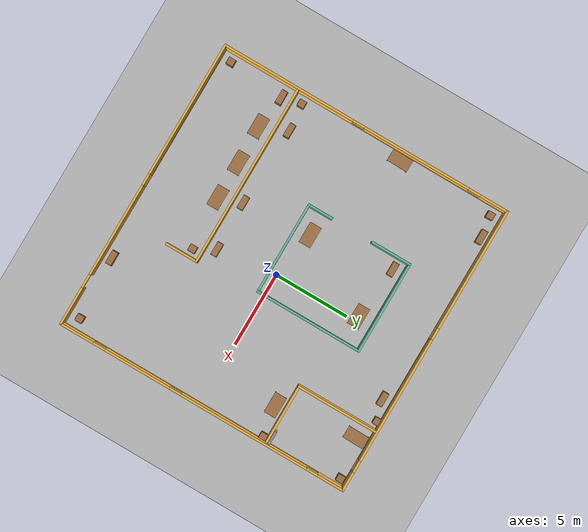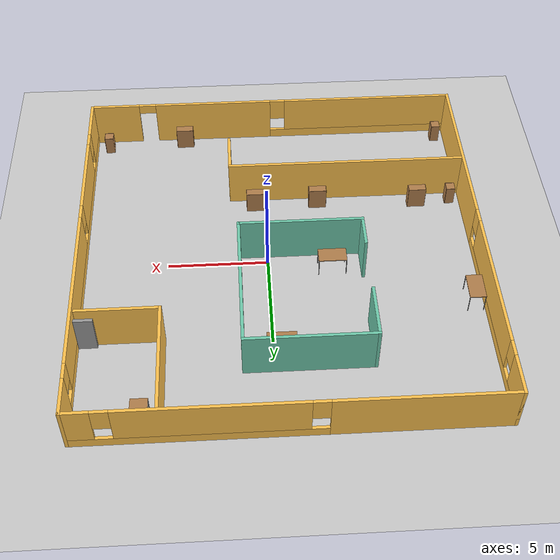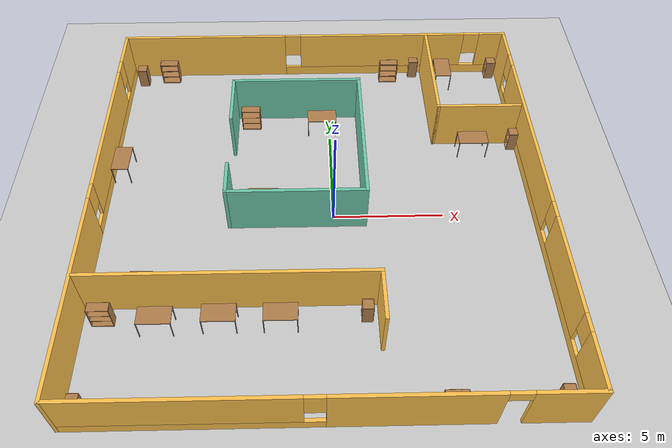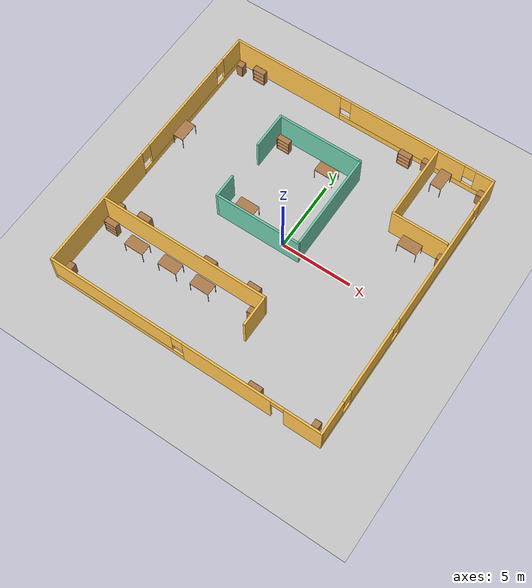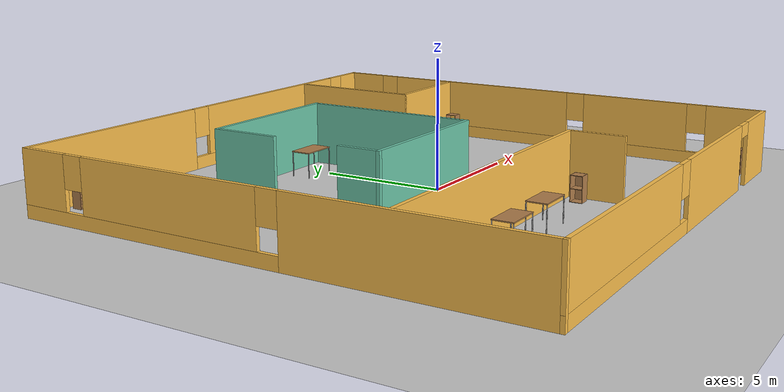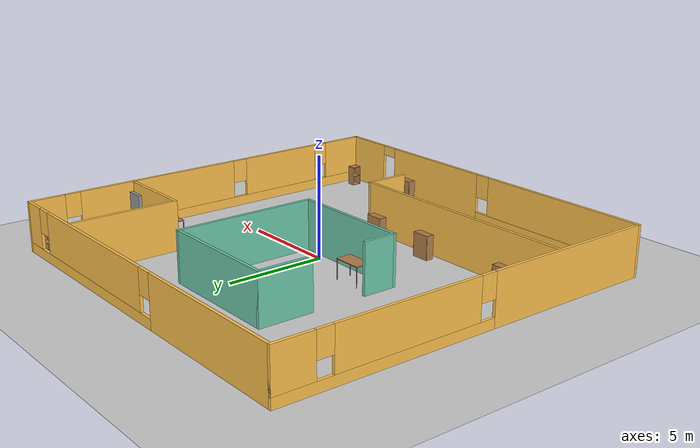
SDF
<sdf version="1.6">
 <world name="default">
  <light name="sun" type="directional">
   <pose>0 0 10 0 -0 0</pose>
   <diffuse>0.8 0.8 0.8 1</diffuse>
   <specular>0.1 0.1 0.1 1</specular>
   <attenuation>
    <range>1000</range>
    <constant>0.9</constant>
    <linear>0.01</linear>
    <quadratic>0.001</quadratic>
   </attenuation>
   <direction>-0.5 0.5 -1</direction>
  </light>
  <model name="ground_plane">
   <static>1</static>
   <link name="link">
    <collision name="collision">
     <geometry><plane><normal>0 0 1</normal><size>100 100</size></plane></geometry>
     <surface><friction><ode><mu>100</mu><mu2>50</mu2></ode></friction></surface>
    </collision>
    <visual name="visual">
     <cast_shadows>0</cast_shadows>
     <geometry><plane><normal>0 0 1</normal><size>100 100</size></plane></geometry>
     <material>
      <script><uri>file://media/materials/scripts/gazebo.material</uri><name>Gazebo/Grey</name></script>
     </material>
    </visual>
   </link>
  </model>
  <gravity>0 0 -9.8</gravity>
  <magnetic_field>6e-06 2.3e-05 -4.2e-05</magnetic_field>
  <atmosphere type="adiabatic"/>
  <physics name="default_physics" default="0" type="ode">
   <max_step_size>0.001</max_step_size>
   <real_time_factor>1</real_time_factor>
   <real_time_update_rate>1000</real_time_update_rate>
  </physics>
  <scene><ambient>0.4 0.4 0.4 1</ambient><background>0.7 0.7 0.7 1</background><shadows>1</shadows></scene>
  <spherical_coordinates>
   <surface_model>EARTH_WGS84</surface_model>
   <latitude_deg>0</latitude_deg>
   <longitude_deg>0</longitude_deg>
   <elevation>0</elevation>
   <heading_deg>0</heading_deg>
  </spherical_coordinates>
  <model name="better_office">
   <pose>-0.62787 0.18736 0 0 -0 0</pose>
   <link name="Door_0">
    <collision name="Door_0_Collision">
     <geometry><box><size>0.9 0.17 2</size></box></geometry>
     <pose>0 0 1 0 -0 0</pose>
    </collision>
    <visual name="Door_0_Visual">
     <pose>0 0 1 0 -0 0</pose>
     <geometry><box><size>0.9 0.17 2</size></box></geometry>
     <material>
      <script><uri>file://media/materials/scripts/gazebo.material</uri><name>Gazebo/Grey</name></script>
     </material>
    </visual>
    <pose>9.27377 4.6409 0 0 -0 0</pose>
   </link>
   <link name="Wall_11">
    <pose>0 9.925 0 0 -0 0</pose>
    <visual name="Wall_11_Visual_0">
     <pose>-5.73664 0 1.25 0 -0 0</pose>
     <geometry><box><size>8.27672 0.15 2.5</size></box></geometry>
     <material>
      <script><uri>file://media/materials/scripts/gazebo.material</uri><name>Gazebo/Grey</name></script>
      <ambient>1 0.764706 0.305882 1</ambient>
     </material>
    </visual>
    <collision name="Wall_11_Collision_0">
     <geometry><box><size>8.27672 0.15 2.5</size></box></geometry>
     <pose>-5.73664 0 1.25 0 -0 0</pose>
    </collision>
    <visual name="Wall_11_Visual_1">
     <pose>4.13836 0 0.25 0 -0 0</pose>
     <geometry><box><size>11.4733 0.15 0.5</size></box></geometry>
     <material>
      <script><uri>file://media/materials/scripts/gazebo.material</uri><name>Gazebo/Grey</name></script>
      <ambient>1 0.764706 0.305882 1</ambient>
     </material>
    </visual>
    <collision name="Wall_11_Collision_1">
     <geometry><box><size>11.4733 0.15 0.5</size></box></geometry>
     <pose>4.13836 0 0.25 0 -0 0</pose>
    </collision>
    <visual name="Wall_11_Visual_2">
     <pose>3.47169 0 1.5 0 -0 0</pose>
     <geometry><box><size>8.53993 0.15 2</size></box></geometry>
     <material>
      <script><uri>file://media/materials/scripts/gazebo.material</uri><name>Gazebo/Grey</name></script>
      <ambient>1 0.764706 0.305882 1</ambient>
     </material>
    </visual>
    <collision name="Wall_11_Collision_2">
     <geometry><box><size>8.53993 0.15 2</size></box></geometry>
     <pose>3.47169 0 1.5 0 -0 0</pose>
    </collision>
    <visual name="Wall_11_Visual_3">
     <pose>9.20833 0 1.5 0 -0 0</pose>
     <geometry><box><size>1.33335 0.15 2</size></box></geometry>
     <material>
      <script><uri>file://media/materials/scripts/gazebo.material</uri><name>Gazebo/Grey</name></script>
      <ambient>1 0.764706 0.305882 1</ambient>
     </material>
    </visual>
    <collision name="Wall_11_Collision_3">
     <geometry><box><size>1.33335 0.15 2</size></box></geometry>
     <pose>9.20833 0 1.5 0 -0 0</pose>
    </collision>
    <visual name="Wall_11_Visual_4">
     <pose>-1.19828 0 1.9 0 -0 0</pose>
     <geometry><box><size>0.8 0.15 1.2</size></box></geometry>
     <material>
      <script><uri>file://media/materials/scripts/gazebo.material</uri><name>Gazebo/Grey</name></script>
      <ambient>1 0.764706 0.305882 1</ambient>
     </material>
    </visual>
    <collision name="Wall_11_Collision_4">
     <geometry><box><size>0.8 0.15 1.2</size></box></geometry>
     <pose>-1.19828 0 1.9 0 -0 0</pose>
    </collision>
    <visual name="Wall_11_Visual_5">
     <pose>8.14165 0 1.9 0 -0 0</pose>
     <geometry><box><size>0.8 0.15 1.2</size></box></geometry>
     <material>
      <script><uri>file://media/materials/scripts/gazebo.material</uri><name>Gazebo/Grey</name></script>
      <ambient>1 0.764706 0.305882 1</ambient>
     </material>
    </visual>
    <collision name="Wall_11_Collision_5">
     <geometry><box><size>0.8 0.15 1.2</size></box></geometry>
     <pose>8.14165 0 1.9 0 -0 0</pose>
    </collision>
   </link>
   <link name="Wall_12">
    <pose>9.8 0 0 0 0 -1.5708</pose>
    <visual name="Wall_12_Visual_0">
     <pose>-9.07711 0 1.25 0 -0 0</pose>
     <geometry><box><size>1.84579 0.15 2.5</size></box></geometry>
     <material>
      <script><uri>file://media/materials/scripts/gazebo.material</uri><name>Gazebo/Grey</name></script>
      <ambient>1 0.764706 0.305882 1</ambient>
     </material>
    </visual>
    <collision name="Wall_12_Collision_0">
     <geometry><box><size>1.84579 0.15 2.5</size></box></geometry>
     <pose>-9.07711 0 1.25 0 -0 0</pose>
    </collision>
    <visual name="Wall_12_Visual_1">
     <pose>0.922894 0 0.25 0 -0 0</pose>
     <geometry><box><size>18.1542 0.15 0.5</size></box></geometry>
     <material>
      <script><uri>file://media/materials/scripts/gazebo.material</uri><name>Gazebo/Grey</name></script>
      <ambient>1 0.764706 0.305882 1</ambient>
     </material>
    </visual>
    <collision name="Wall_12_Collision_1">
     <geometry><box><size>18.1542 0.15 0.5</size></box></geometry>
     <pose>0.922894 0 0.25 0 -0 0</pose>
    </collision>
    <visual name="Wall_12_Visual_2">
     <pose>-2.94273 0 1.5 0 -0 0</pose>
     <geometry><box><size>8.82296 0.15 2</size></box></geometry>
     <material>
      <script><uri>file://media/materials/scripts/gazebo.material</uri><name>Gazebo/Grey</name></script>
      <ambient>1 0.764706 0.305882 1</ambient>
     </material>
    </visual>
    <collision name="Wall_12_Collision_2">
     <geometry><box><size>8.82296 0.15 2</size></box></geometry>
     <pose>-2.94273 0 1.5 0 -0 0</pose>
    </collision>
    <visual name="Wall_12_Visual_3">
     <pose>4.55752 0 1.5 0 -0 0</pose>
     <geometry><box><size>4.57754 0.15 2</size></box></geometry>
     <material>
      <script><uri>file://media/materials/scripts/gazebo.material</uri><name>Gazebo/Grey</name></script>
      <ambient>1 0.764706 0.305882 1</ambient>
     </material>
    </visual>
    <collision name="Wall_12_Collision_3">
     <geometry><box><size>4.57754 0.15 2</size></box></geometry>
     <pose>4.55752 0 1.5 0 -0 0</pose>
    </collision>
    <visual name="Wall_12_Visual_4">
     <pose>8.82314 0 1.5 0 -0 0</pose>
     <geometry><box><size>2.35371 0.15 2</size></box></geometry>
     <material>
      <script><uri>file://media/materials/scripts/gazebo.material</uri><name>Gazebo/Grey</name></script>
      <ambient>1 0.764706 0.305882 1</ambient>
     </material>
    </visual>
    <collision name="Wall_12_Collision_4">
     <geometry><box><size>2.35371 0.15 2</size></box></geometry>
     <pose>8.82314 0 1.5 0 -0 0</pose>
    </collision>
    <visual name="Wall_12_Visual_5">
     <pose>-7.75421 0 1.9 0 -0 0</pose>
     <geometry><box><size>0.8 0.15 1.2</size></box></geometry>
     <material>
      <script><uri>file://media/materials/scripts/gazebo.material</uri><name>Gazebo/Grey</name></script>
      <ambient>1 0.764706 0.305882 1</ambient>
     </material>
    </visual>
    <collision name="Wall_12_Collision_5">
     <geometry><box><size>0.8 0.15 1.2</size></box></geometry>
     <pose>-7.75421 0 1.9 0 -0 0</pose>
    </collision>
    <visual name="Wall_12_Visual_6">
     <pose>1.86875 0 1.9 0 -0 0</pose>
     <geometry><box><size>0.8 0.15 1.2</size></box></geometry>
     <material>
      <script><uri>file://media/materials/scripts/gazebo.material</uri><name>Gazebo/Grey</name></script>
      <ambient>1 0.764706 0.305882 1</ambient>
     </material>
    </visual>
    <collision name="Wall_12_Collision_6">
     <geometry><box><size>0.8 0.15 1.2</size></box></geometry>
     <pose>1.86875 0 1.9 0 -0 0</pose>
    </collision>
    <visual name="Wall_12_Visual_7">
     <pose>7.24629 0 1.9 0 -0 0</pose>
     <geometry><box><size>0.8 0.15 1.2</size></box></geometry>
     <material>
      <script><uri>file://media/materials/scripts/gazebo.material</uri><name>Gazebo/Grey</name></script>
      <ambient>1 0.764706 0.305882 1</ambient>
     </material>
    </visual>
    <collision name="Wall_12_Collision_7">
     <geometry><box><size>0.8 0.15 1.2</size></box></geometry>
     <pose>7.24629 0 1.9 0 -0 0</pose>
    </collision>
   </link>
   <link name="Wall_13">
    <pose>0 -9.925 0 0 -0 3.14159</pose>
    <visual name="Wall_13_Visual_0">
     <pose>-8.56113 0 1.25 0 -0 0</pose>
     <geometry><box><size>2.62773 0.15 2.5</size></box></geometry>
     <material>
      <script><uri>file://media/materials/scripts/gazebo.material</uri><name>Gazebo/Grey</name></script>
      <ambient>1 0.764706 0.305882 1</ambient>
     </material>
    </visual>
    <collision name="Wall_13_Collision_0">
     <geometry><box><size>2.62773 0.15 2.5</size></box></geometry>
     <pose>-8.56113 0 1.25 0 -0 0</pose>
    </collision>
    <visual name="Wall_13_Visual_1">
     <pose>-3.19904 0 1.25 0 -0 0</pose>
     <geometry><box><size>6.29646 0.15 2.5</size></box></geometry>
     <material>
      <script><uri>file://media/materials/scripts/gazebo.material</uri><name>Gazebo/Grey</name></script>
      <ambient>1 0.764706 0.305882 1</ambient>
     </material>
    </visual>
    <collision name="Wall_13_Collision_1">
     <geometry><box><size>6.29646 0.15 2.5</size></box></geometry>
     <pose>-3.19904 0 1.25 0 -0 0</pose>
    </collision>
    <visual name="Wall_13_Visual_2">
     <pose>4.9121 0 0.25 0 -0 0</pose>
     <geometry><box><size>9.92581 0.15 0.5</size></box></geometry>
     <material>
      <script><uri>file://media/materials/scripts/gazebo.material</uri><name>Gazebo/Grey</name></script>
      <ambient>1 0.764706 0.305882 1</ambient>
     </material>
    </visual>
    <collision name="Wall_13_Collision_2">
     <geometry><box><size>9.92581 0.15 0.5</size></box></geometry>
     <pose>4.9121 0 0.25 0 -0 0</pose>
    </collision>
    <visual name="Wall_13_Visual_3">
     <pose>5.3121 0 1.5 0 -0 0</pose>
     <geometry><box><size>9.12581 0.15 2</size></box></geometry>
     <material>
      <script><uri>file://media/materials/scripts/gazebo.material</uri><name>Gazebo/Grey</name></script>
      <ambient>1 0.764706 0.305882 1</ambient>
     </material>
    </visual>
    <collision name="Wall_13_Collision_3">
     <geometry><box><size>9.12581 0.15 2</size></box></geometry>
     <pose>5.3121 0 1.5 0 -0 0</pose>
    </collision>
    <visual name="Wall_13_Visual_4">
     <pose>0.349194 0 1.9 0 -0 0</pose>
     <geometry><box><size>0.8 0.15 1.2</size></box></geometry>
     <material>
      <script><uri>file://media/materials/scripts/gazebo.material</uri><name>Gazebo/Grey</name></script>
      <ambient>1 0.764706 0.305882 1</ambient>
     </material>
    </visual>
    <collision name="Wall_13_Collision_4">
     <geometry><box><size>0.8 0.15 1.2</size></box></geometry>
     <pose>0.349194 0 1.9 0 -0 0</pose>
    </collision>
    <visual name="Wall_13_Visual_5">
     <pose>-6.79727 0 2.25 0 -0 0</pose>
     <geometry><box><size>0.9 0.15 0.5</size></box></geometry>
     <material>
      <script><uri>file://media/materials/scripts/gazebo.material</uri><name>Gazebo/Grey</name></script>
      <ambient>1 0.764706 0.305882 1</ambient>
     </material>
    </visual>
    <collision name="Wall_13_Collision_5">
     <geometry><box><size>0.9 0.15 0.5</size></box></geometry>
     <pose>-6.79727 0 2.25 0 -0 0</pose>
    </collision>
   </link>
   <link name="Wall_14">
    <pose>-9.8 0 0 0 -0 1.5708</pose>
    <visual name="Wall_14_Visual_0">
     <pose>-5.46218 0 1.25 0 -0 0</pose>
     <geometry><box><size>9.07564 0.15 2.5</size></box></geometry>
     <material>
      <script><uri>file://media/materials/scripts/gazebo.material</uri><name>Gazebo/Grey</name></script>
      <ambient>1 0.764706 0.305882 1</ambient>
     </material>
    </visual>
    <collision name="Wall_14_Collision_0">
     <geometry><box><size>9.07564 0.15 2.5</size></box></geometry>
     <pose>-5.46218 0 1.25 0 -0 0</pose>
    </collision>
    <visual name="Wall_14_Visual_1">
     <pose>4.53782 0 0.25 0 -0 0</pose>
     <geometry><box><size>10.9244 0.15 0.5</size></box></geometry>
     <material>
      <script><uri>file://media/materials/scripts/gazebo.material</uri><name>Gazebo/Grey</name></script>
      <ambient>1 0.764706 0.305882 1</ambient>
     </material>
    </visual>
    <collision name="Wall_14_Collision_1">
     <geometry><box><size>10.9244 0.15 0.5</size></box></geometry>
     <pose>4.53782 0 0.25 0 -0 0</pose>
    </collision>
    <visual name="Wall_14_Visual_2">
     <pose>3.54417 0 1.5 0 -0 0</pose>
     <geometry><box><size>7.33706 0.15 2</size></box></geometry>
     <material>
      <script><uri>file://media/materials/scripts/gazebo.material</uri><name>Gazebo/Grey</name></script>
      <ambient>1 0.764706 0.305882 1</ambient>
     </material>
    </visual>
    <collision name="Wall_14_Collision_2">
     <geometry><box><size>7.33706 0.15 2</size></box></geometry>
     <pose>3.54417 0 1.5 0 -0 0</pose>
    </collision>
    <visual name="Wall_14_Visual_3">
     <pose>9.00635 0 1.5 0 -0 0</pose>
     <geometry><box><size>1.9873 0.15 2</size></box></geometry>
     <material>
      <script><uri>file://media/materials/scripts/gazebo.material</uri><name>Gazebo/Grey</name></script>
      <ambient>1 0.764706 0.305882 1</ambient>
     </material>
    </visual>
    <collision name="Wall_14_Collision_3">
     <geometry><box><size>1.9873 0.15 2</size></box></geometry>
     <pose>9.00635 0 1.5 0 -0 0</pose>
    </collision>
    <visual name="Wall_14_Visual_4">
     <pose>-0.524364 0 1.9 0 -0 0</pose>
     <geometry><box><size>0.8 0.15 1.2</size></box></geometry>
     <material>
      <script><uri>file://media/materials/scripts/gazebo.material</uri><name>Gazebo/Grey</name></script>
      <ambient>1 0.764706 0.305882 1</ambient>
     </material>
    </visual>
    <collision name="Wall_14_Collision_4">
     <geometry><box><size>0.8 0.15 1.2</size></box></geometry>
     <pose>-0.524364 0 1.9 0 -0 0</pose>
    </collision>
    <visual name="Wall_14_Visual_5">
     <pose>7.6127 0 1.9 0 -0 0</pose>
     <geometry><box><size>0.8 0.15 1.2</size></box></geometry>
     <material>
      <script><uri>file://media/materials/scripts/gazebo.material</uri><name>Gazebo/Grey</name></script>
      <ambient>1 0.764706 0.305882 1</ambient>
     </material>
    </visual>
    <collision name="Wall_14_Collision_5">
     <geometry><box><size>0.8 0.15 1.2</size></box></geometry>
     <pose>7.6127 0 1.9 0 -0 0</pose>
    </collision>
   </link>
   <link name="Wall_17">
    <collision name="Wall_17_Collision">
     <geometry><box><size>2.75 0.15 2.5</size></box></geometry>
     <pose>0 0 1.25 0 -0 0</pose>
    </collision>
    <visual name="Wall_17_Visual">
     <pose>0 0 1.25 0 -0 0</pose>
     <geometry><box><size>2.75 0.15 2.5</size></box></geometry>
     <material>
      <script><uri>file://media/materials/scripts/gazebo.material</uri><name>Gazebo/Grey</name></script>
      <ambient>0.435294 0.796078 0.67451 1</ambient>
     </material>
    </visual>
    <pose>-4.0561 5.16257 0 0 -0 1.5708</pose>
   </link>
   <link name="Wall_18">
    <collision name="Wall_18_Collision">
     <geometry><box><size>6.25 0.15 2.5</size></box></geometry>
     <pose>0 0 1.25 0 -0 0</pose>
    </collision>
    <visual name="Wall_18_Visual">
     <pose>0 0 1.25 0 -0 0</pose>
     <geometry><box><size>6.25 0.15 2.5</size></box></geometry>
     <material>
      <script><uri>file://media/materials/scripts/gazebo.material</uri><name>Gazebo/Grey</name></script>
      <ambient>0.435294 0.796078 0.67451 1</ambient>
     </material>
    </visual>
    <pose>-1.0061 6.46257 0 0 -0 0</pose>
   </link>
   <link name="Wall_19">
    <collision name="Wall_19_Collision">
     <geometry><box><size>7.25 0.15 2.5</size></box></geometry>
     <pose>0 0 1.25 0 -0 0</pose>
    </collision>
    <visual name="Wall_19_Visual">
     <pose>0 0 1.25 0 -0 0</pose>
     <geometry><box><size>7.25 0.15 2.5</size></box></geometry>
     <material>
      <script><uri>file://media/materials/scripts/gazebo.material</uri><name>Gazebo/Grey</name></script>
      <ambient>0.435294 0.796078 0.67451 1</ambient>
     </material>
    </visual>
    <pose>2.0439 2.91257 0 0 0 -1.5708</pose>
   </link>
   <link name="Wall_20">
    <collision name="Wall_20_Collision">
     <geometry><box><size>6.25 0.15 2.5</size></box></geometry>
     <pose>0 0 1.25 0 -0 0</pose>
    </collision>
    <visual name="Wall_20_Visual">
     <pose>0 0 1.25 0 -0 0</pose>
     <geometry><box><size>6.25 0.15 2.5</size></box></geometry>
     <material>
      <script><uri>file://media/materials/scripts/gazebo.material</uri><name>Gazebo/Grey</name></script>
      <ambient>0.435294 0.796078 0.67451 1</ambient>
     </material>
    </visual>
    <pose>-1.0061 -0.637427 0 0 -0 3.14159</pose>
   </link>
   <link name="Wall_21">
    <collision name="Wall_21_Collision">
     <geometry><box><size>1.75 0.15 2.5</size></box></geometry>
     <pose>0 0 1.25 0 -0 0</pose>
    </collision>
    <visual name="Wall_21_Visual">
     <pose>0 0 1.25 0 -0 0</pose>
     <geometry><box><size>1.75 0.15 2.5</size></box></geometry>
     <material>
      <script><uri>file://media/materials/scripts/gazebo.material</uri><name>Gazebo/Grey</name></script>
      <ambient>0.435294 0.796078 0.67451 1</ambient>
     </material>
    </visual>
    <pose>-4.0561 0.162573 0 0 -0 1.5708</pose>
   </link>
   <link name="Wall_23">
    <collision name="Wall_23_Collision">
     <geometry><box><size>12.2123 0.15 2.5</size></box></geometry>
     <pose>0 0 1.25 0 -0 0</pose>
    </collision>
    <visual name="Wall_23_Visual">
     <pose>0 0 1.25 0 -0 0</pose>
     <geometry><box><size>12.2123 0.15 2.5</size></box></geometry>
     <material>
      <script><uri>file://media/materials/scripts/gazebo.material</uri><name>Gazebo/Grey</name></script>
      <ambient>1 0.764706 0.305882 1</ambient>
     </material>
    </visual>
    <pose>-3.65799 -4.76979 0 0 -0 0</pose>
   </link>
   <link name="Wall_26">
    <collision name="Wall_26_Collision">
     <geometry><box><size>5.5 0.15 2.5</size></box></geometry>
     <pose>0 0 1.25 0 -0 0</pose>
    </collision>
    <visual name="Wall_26_Visual">
     <pose>0 0 1.25 0 -0 0</pose>
     <geometry><box><size>5.5 0.15 2.5</size></box></geometry>
     <material>
      <script><uri>file://media/materials/scripts/gazebo.material</uri><name>Gazebo/Grey</name></script>
      <ambient>1 0.764706 0.305882 1</ambient>
     </material>
    </visual>
    <pose>5.73591 7.13117 0 0 0 -1.5708</pose>
   </link>
   <link name="Wall_27">
    <collision name="Wall_27_Collision">
     <geometry><box><size>4 0.15 2.5</size></box></geometry>
     <pose>0 0 1.25 0 -0 0</pose>
    </collision>
    <visual name="Wall_27_Visual">
     <pose>0 0 1.25 0 -0 0</pose>
     <geometry><box><size>4 0.15 2.5</size></box></geometry>
     <material>
      <script><uri>file://media/materials/scripts/gazebo.material</uri><name>Gazebo/Grey</name></script>
      <ambient>1 0.764706 0.305882 1</ambient>
     </material>
    </visual>
    <pose>7.66091 4.45617 0 0 -0 0</pose>
   </link>
   <link name="Wall_29">
    <collision name="Wall_29_Collision">
     <geometry><box><size>2.25 0.15 2.5</size></box></geometry>
     <pose>0 0 1.25 0 -0 0</pose>
    </collision>
    <visual name="Wall_29_Visual">
     <pose>0 0 1.25 0 -0 0</pose>
     <geometry><box><size>2.25 0.15 2.5</size></box></geometry>
     <material>
      <script><uri>file://media/materials/scripts/gazebo.material</uri><name>Gazebo/Grey</name></script>
      <ambient>1 0.764706 0.305882 1</ambient>
     </material>
    </visual>
    <pose>2.37315 -5.81979 0 0 0 -1.5708</pose>
   </link>
   <static>1</static>
  </model>
  <model name="cabinet">
   <static>1</static>
   <link name="cabinet_bottom_plate">
    <inertial>
     <pose>0 0 -1 0 -0 0</pose>
     <inertia><ixx>2.05</ixx><ixy>0</ixy><ixz>0</ixz><iyy>2.05</iyy><iyz>0</iyz><izz>2.05</izz></inertia>
     <mass>25</mass>
    </inertial>
    <collision name="cabinet_bottom_plate_geom">
     <pose>0 0 0.01 0 -0 0</pose>
     <geometry><box><size>0.45 0.45 0.02</size></box></geometry>
    </collision>
    <visual name="cabinet_bottom_plate_geom_visual">
     <pose>0 0 0.01 0 -0 0</pose>
     <geometry><box><size>0.45 0.45 0.02</size></box></geometry>
     <material>
      <script><uri>file://media/materials/scripts/gazebo.material</uri><name>Gazebo/Wood</name></script>
     </material>
    </visual>
    <collision name="cabinet_bottom_plate_geom_cabinet_back_plate">
     <pose>0.235 0 0.51 0 -0 0</pose>
     <geometry><box><size>0.02 0.45 1.02</size></box></geometry>
    </collision>
    <visual name="cabinet_bottom_plate_geom_cabinet_back_plate_visual">
     <pose>0.235 0 0.51 0 -0 0</pose>
     <geometry><box><size>0.02 0.45 1.02</size></box></geometry>
     <material>
      <script><uri>file://media/materials/scripts/gazebo.material</uri><name>Gazebo/Wood</name></script>
     </material>
    </visual>
    <collision name="cabinet_bottom_plate_geom_cabinet_left_plate">
     <pose>0 0.235 0.51 0 -0 0</pose>
     <geometry><box><size>0.45 0.02 1.02</size></box></geometry>
    </collision>
    <visual name="cabinet_bottom_plate_geom_cabinet_left_plate_visual">
     <pose>0 0.235 0.51 0 -0 0</pose>
     <geometry><box><size>0.45 0.02 1.02</size></box></geometry>
     <material>
      <script><uri>file://media/materials/scripts/gazebo.material</uri><name>Gazebo/Wood</name></script>
     </material>
    </visual>
    <collision name="cabinet_bottom_plate_geom_cabinet_middle_plate">
     <pose>0 0 0.51 0 -0 0</pose>
     <geometry><box><size>0.45 0.45 0.02</size></box></geometry>
    </collision>
    <visual name="cabinet_bottom_plate_geom_cabinet_middle_plate_visual">
     <pose>0 0 0.51 0 -0 0</pose>
     <geometry><box><size>0.45 0.45 0.02</size></box></geometry>
     <material>
      <script><uri>file://media/materials/scripts/gazebo.material</uri><name>Gazebo/Wood</name></script>
     </material>
    </visual>
    <collision name="cabinet_bottom_plate_geom_cabinet_right_plate">
     <pose>0 -0.235 0.51 0 -0 0</pose>
     <geometry><box><size>0.45 0.02 1.02</size></box></geometry>
    </collision>
    <visual name="cabinet_bottom_plate_geom_cabinet_right_plate_visual">
     <pose>0 -0.235 0.51 0 -0 0</pose>
     <geometry><box><size>0.45 0.02 1.02</size></box></geometry>
     <material>
      <script><uri>file://media/materials/scripts/gazebo.material</uri><name>Gazebo/Wood</name></script>
     </material>
    </visual>
    <collision name="cabinet_bottom_plate_geom_cabinet_top_plate">
     <pose>0 0 1.01 0 -0 0</pose>
     <geometry><box><size>0.45 0.45 0.02</size></box></geometry>
    </collision>
    <visual name="cabinet_bottom_plate_geom_cabinet_top_plate_visual">
     <pose>0 0 1.01 0 -0 0</pose>
     <geometry><box><size>0.45 0.45 0.02</size></box></geometry>
     <material>
      <script><uri>file://media/materials/scripts/gazebo.material</uri><name>Gazebo/Wood</name></script>
     </material>
    </visual>
   </link>
   <pose>-9.81477 9.43593 0 0 -0 0</pose>
  </model>
  <model name="cabinet_clone">
   <static>1</static>
   <link name="cabinet_bottom_plate">
    <inertial>
     <pose>0 0 -1 0 -0 0</pose>
     <inertia><ixx>2.05</ixx><ixy>0</ixy><ixz>0</ixz><iyy>2.05</iyy><iyz>0</iyz><izz>2.05</izz></inertia>
     <mass>25</mass>
    </inertial>
    <collision name="cabinet_bottom_plate_geom">
     <pose>0 0 0.01 0 -0 0</pose>
     <geometry><box><size>0.45 0.45 0.02</size></box></geometry>
    </collision>
    <visual name="cabinet_bottom_plate_geom_visual">
     <pose>0 0 0.01 0 -0 0</pose>
     <geometry><box><size>0.45 0.45 0.02</size></box></geometry>
     <material>
      <script><uri>file://media/materials/scripts/gazebo.material</uri><name>Gazebo/Wood</name></script>
     </material>
    </visual>
    <collision name="cabinet_bottom_plate_geom_cabinet_back_plate">
     <pose>0.235 0 0.51 0 -0 0</pose>
     <geometry><box><size>0.02 0.45 1.02</size></box></geometry>
    </collision>
    <visual name="cabinet_bottom_plate_geom_cabinet_back_plate_visual">
     <pose>0.235 0 0.51 0 -0 0</pose>
     <geometry><box><size>0.02 0.45 1.02</size></box></geometry>
     <material>
      <script><uri>file://media/materials/scripts/gazebo.material</uri><name>Gazebo/Wood</name></script>
     </material>
    </visual>
    <collision name="cabinet_bottom_plate_geom_cabinet_left_plate">
     <pose>0 0.235 0.51 0 -0 0</pose>
     <geometry><box><size>0.45 0.02 1.02</size></box></geometry>
    </collision>
    <visual name="cabinet_bottom_plate_geom_cabinet_left_plate_visual">
     <pose>0 0.235 0.51 0 -0 0</pose>
     <geometry><box><size>0.45 0.02 1.02</size></box></geometry>
     <material>
      <script><uri>file://media/materials/scripts/gazebo.material</uri><name>Gazebo/Wood</name></script>
     </material>
    </visual>
    <collision name="cabinet_bottom_plate_geom_cabinet_middle_plate">
     <pose>0 0 0.51 0 -0 0</pose>
     <geometry><box><size>0.45 0.45 0.02</size></box></geometry>
    </collision>
    <visual name="cabinet_bottom_plate_geom_cabinet_middle_plate_visual">
     <pose>0 0 0.51 0 -0 0</pose>
     <geometry><box><size>0.45 0.45 0.02</size></box></geometry>
     <material>
      <script><uri>file://media/materials/scripts/gazebo.material</uri><name>Gazebo/Wood</name></script>
     </material>
    </visual>
    <collision name="cabinet_bottom_plate_geom_cabinet_right_plate">
     <pose>0 -0.235 0.51 0 -0 0</pose>
     <geometry><box><size>0.45 0.02 1.02</size></box></geometry>
    </collision>
    <visual name="cabinet_bottom_plate_geom_cabinet_right_plate_visual">
     <pose>0 -0.235 0.51 0 -0 0</pose>
     <geometry><box><size>0.45 0.02 1.02</size></box></geometry>
     <material>
      <script><uri>file://media/materials/scripts/gazebo.material</uri><name>Gazebo/Wood</name></script>
     </material>
    </visual>
    <collision name="cabinet_bottom_plate_geom_cabinet_top_plate">
     <pose>0 0 1.01 0 -0 0</pose>
     <geometry><box><size>0.45 0.45 0.02</size></box></geometry>
    </collision>
    <visual name="cabinet_bottom_plate_geom_cabinet_top_plate_visual">
     <pose>0 0 1.01 0 -0 0</pose>
     <geometry><box><size>0.45 0.45 0.02</size></box></geometry>
     <material>
      <script><uri>file://media/materials/scripts/gazebo.material</uri><name>Gazebo/Wood</name></script>
     </material>
    </visual>
   </link>
   <pose>-9.82401 -3.98425 0 0 -0 0</pose>
  </model>
  <model name="cabinet_clone_0">
   <static>1</static>
   <link name="cabinet_bottom_plate">
    <inertial>
     <pose>0 0 -1 0 -0 0</pose>
     <inertia><ixx>2.05</ixx><ixy>0</ixy><ixz>0</ixz><iyy>2.05</iyy><iyz>0</iyz><izz>2.05</izz></inertia>
     <mass>25</mass>
    </inertial>
    <collision name="cabinet_bottom_plate_geom">
     <pose>0 0 0.01 0 -0 0</pose>
     <geometry><box><size>0.45 0.45 0.02</size></box></geometry>
    </collision>
    <visual name="cabinet_bottom_plate_geom_visual">
     <pose>0 0 0.01 0 -0 0</pose>
     <geometry><box><size>0.45 0.45 0.02</size></box></geometry>
     <material>
      <script><uri>file://media/materials/scripts/gazebo.material</uri><name>Gazebo/Wood</name></script>
     </material>
    </visual>
    <collision name="cabinet_bottom_plate_geom_cabinet_back_plate">
     <pose>0.235 0 0.51 0 -0 0</pose>
     <geometry><box><size>0.02 0.45 1.02</size></box></geometry>
    </collision>
    <visual name="cabinet_bottom_plate_geom_cabinet_back_plate_visual">
     <pose>0.235 0 0.51 0 -0 0</pose>
     <geometry><box><size>0.02 0.45 1.02</size></box></geometry>
     <material>
      <script><uri>file://media/materials/scripts/gazebo.material</uri><name>Gazebo/Wood</name></script>
     </material>
    </visual>
    <collision name="cabinet_bottom_plate_geom_cabinet_left_plate">
     <pose>0 0.235 0.51 0 -0 0</pose>
     <geometry><box><size>0.45 0.02 1.02</size></box></geometry>
    </collision>
    <visual name="cabinet_bottom_plate_geom_cabinet_left_plate_visual">
     <pose>0 0.235 0.51 0 -0 0</pose>
     <geometry><box><size>0.45 0.02 1.02</size></box></geometry>
     <material>
      <script><uri>file://media/materials/scripts/gazebo.material</uri><name>Gazebo/Wood</name></script>
     </material>
    </visual>
    <collision name="cabinet_bottom_plate_geom_cabinet_middle_plate">
     <pose>0 0 0.51 0 -0 0</pose>
     <geometry><box><size>0.45 0.45 0.02</size></box></geometry>
    </collision>
    <visual name="cabinet_bottom_plate_geom_cabinet_middle_plate_visual">
     <pose>0 0 0.51 0 -0 0</pose>
     <geometry><box><size>0.45 0.45 0.02</size></box></geometry>
     <material>
      <script><uri>file://media/materials/scripts/gazebo.material</uri><name>Gazebo/Wood</name></script>
     </material>
    </visual>
    <collision name="cabinet_bottom_plate_geom_cabinet_right_plate">
     <pose>0 -0.235 0.51 0 -0 0</pose>
     <geometry><box><size>0.45 0.02 1.02</size></box></geometry>
    </collision>
    <visual name="cabinet_bottom_plate_geom_cabinet_right_plate_visual">
     <pose>0 -0.235 0.51 0 -0 0</pose>
     <geometry><box><size>0.45 0.02 1.02</size></box></geometry>
     <material>
      <script><uri>file://media/materials/scripts/gazebo.material</uri><name>Gazebo/Wood</name></script>
     </material>
    </visual>
    <collision name="cabinet_bottom_plate_geom_cabinet_top_plate">
     <pose>0 0 1.01 0 -0 0</pose>
     <geometry><box><size>0.45 0.45 0.02</size></box></geometry>
    </collision>
    <visual name="cabinet_bottom_plate_geom_cabinet_top_plate_visual">
     <pose>0 0 1.01 0 -0 0</pose>
     <geometry><box><size>0.45 0.45 0.02</size></box></geometry>
     <material>
      <script><uri>file://media/materials/scripts/gazebo.material</uri><name>Gazebo/Wood</name></script>
     </material>
    </visual>
   </link>
   <pose>4.56601 9.88288 0 0 -0 0</pose>
  </model>
  <model name="cabinet_clone_1">
   <static>1</static>
   <link name="cabinet_bottom_plate">
    <inertial>
     <pose>0 0 -1 0 -0 0</pose>
     <inertia><ixx>2.05</ixx><ixy>0</ixy><ixz>0</ixz><iyy>2.05</iyy><iyz>0</iyz><izz>2.05</izz></inertia>
     <mass>25</mass>
    </inertial>
    <collision name="cabinet_bottom_plate_geom">
     <pose>0 0 0.01 0 -0 0</pose>
     <geometry><box><size>0.45 0.45 0.02</size></box></geometry>
    </collision>
    <visual name="cabinet_bottom_plate_geom_visual">
     <pose>0 0 0.01 0 -0 0</pose>
     <geometry><box><size>0.45 0.45 0.02</size></box></geometry>
     <material>
      <script><uri>file://media/materials/scripts/gazebo.material</uri><name>Gazebo/Wood</name></script>
     </material>
    </visual>
    <collision name="cabinet_bottom_plate_geom_cabinet_back_plate">
     <pose>0.235 0 0.51 0 -0 0</pose>
     <geometry><box><size>0.02 0.45 1.02</size></box></geometry>
    </collision>
    <visual name="cabinet_bottom_plate_geom_cabinet_back_plate_visual">
     <pose>0.235 0 0.51 0 -0 0</pose>
     <geometry><box><size>0.02 0.45 1.02</size></box></geometry>
     <material>
      <script><uri>file://media/materials/scripts/gazebo.material</uri><name>Gazebo/Wood</name></script>
     </material>
    </visual>
    <collision name="cabinet_bottom_plate_geom_cabinet_left_plate">
     <pose>0 0.235 0.51 0 -0 0</pose>
     <geometry><box><size>0.45 0.02 1.02</size></box></geometry>
    </collision>
    <visual name="cabinet_bottom_plate_geom_cabinet_left_plate_visual">
     <pose>0 0.235 0.51 0 -0 0</pose>
     <geometry><box><size>0.45 0.02 1.02</size></box></geometry>
     <material>
      <script><uri>file://media/materials/scripts/gazebo.material</uri><name>Gazebo/Wood</name></script>
     </material>
    </visual>
    <collision name="cabinet_bottom_plate_geom_cabinet_middle_plate">
     <pose>0 0 0.51 0 -0 0</pose>
     <geometry><box><size>0.45 0.45 0.02</size></box></geometry>
    </collision>
    <visual name="cabinet_bottom_plate_geom_cabinet_middle_plate_visual">
     <pose>0 0 0.51 0 -0 0</pose>
     <geometry><box><size>0.45 0.45 0.02</size></box></geometry>
     <material>
      <script><uri>file://media/materials/scripts/gazebo.material</uri><name>Gazebo/Wood</name></script>
     </material>
    </visual>
    <collision name="cabinet_bottom_plate_geom_cabinet_right_plate">
     <pose>0 -0.235 0.51 0 -0 0</pose>
     <geometry><box><size>0.45 0.02 1.02</size></box></geometry>
    </collision>
    <visual name="cabinet_bottom_plate_geom_cabinet_right_plate_visual">
     <pose>0 -0.235 0.51 0 -0 0</pose>
     <geometry><box><size>0.45 0.02 1.02</size></box></geometry>
     <material>
      <script><uri>file://media/materials/scripts/gazebo.material</uri><name>Gazebo/Wood</name></script>
     </material>
    </visual>
    <collision name="cabinet_bottom_plate_geom_cabinet_top_plate">
     <pose>0 0 1.01 0 -0 0</pose>
     <geometry><box><size>0.45 0.45 0.02</size></box></geometry>
    </collision>
    <visual name="cabinet_bottom_plate_geom_cabinet_top_plate_visual">
     <pose>0 0 1.01 0 -0 0</pose>
     <geometry><box><size>0.45 0.45 0.02</size></box></geometry>
     <material>
      <script><uri>file://media/materials/scripts/gazebo.material</uri><name>Gazebo/Wood</name></script>
     </material>
    </visual>
   </link>
   <pose>8.71656 9.72479 0 0 -0 0</pose>
  </model>
  <model name="cabinet_clone_2">
   <static>1</static>
   <link name="cabinet_bottom_plate">
    <inertial>
     <pose>0 0 -1 0 -0 0</pose>
     <inertia><ixx>2.05</ixx><ixy>0</ixy><ixz>0</ixz><iyy>2.05</iyy><iyz>0</iyz><izz>2.05</izz></inertia>
     <mass>25</mass>
    </inertial>
    <collision name="cabinet_bottom_plate_geom">
     <pose>0 0 0.01 0 -0 0</pose>
     <geometry><box><size>0.45 0.45 0.02</size></box></geometry>
    </collision>
    <visual name="cabinet_bottom_plate_geom_visual">
     <pose>0 0 0.01 0 -0 0</pose>
     <geometry><box><size>0.45 0.45 0.02</size></box></geometry>
     <material>
      <script><uri>file://media/materials/scripts/gazebo.material</uri><name>Gazebo/Wood</name></script>
     </material>
    </visual>
    <collision name="cabinet_bottom_plate_geom_cabinet_back_plate">
     <pose>0.235 0 0.51 0 -0 0</pose>
     <geometry><box><size>0.02 0.45 1.02</size></box></geometry>
    </collision>
    <visual name="cabinet_bottom_plate_geom_cabinet_back_plate_visual">
     <pose>0.235 0 0.51 0 -0 0</pose>
     <geometry><box><size>0.02 0.45 1.02</size></box></geometry>
     <material>
      <script><uri>file://media/materials/scripts/gazebo.material</uri><name>Gazebo/Wood</name></script>
     </material>
    </visual>
    <collision name="cabinet_bottom_plate_geom_cabinet_left_plate">
     <pose>0 0.235 0.51 0 -0 0</pose>
     <geometry><box><size>0.45 0.02 1.02</size></box></geometry>
    </collision>
    <visual name="cabinet_bottom_plate_geom_cabinet_left_plate_visual">
     <pose>0 0.235 0.51 0 -0 0</pose>
     <geometry><box><size>0.45 0.02 1.02</size></box></geometry>
     <material>
      <script><uri>file://media/materials/scripts/gazebo.material</uri><name>Gazebo/Wood</name></script>
     </material>
    </visual>
    <collision name="cabinet_bottom_plate_geom_cabinet_middle_plate">
     <pose>0 0 0.51 0 -0 0</pose>
     <geometry><box><size>0.45 0.45 0.02</size></box></geometry>
    </collision>
    <visual name="cabinet_bottom_plate_geom_cabinet_middle_plate_visual">
     <pose>0 0 0.51 0 -0 0</pose>
     <geometry><box><size>0.45 0.45 0.02</size></box></geometry>
     <material>
      <script><uri>file://media/materials/scripts/gazebo.material</uri><name>Gazebo/Wood</name></script>
     </material>
    </visual>
    <collision name="cabinet_bottom_plate_geom_cabinet_right_plate">
     <pose>0 -0.235 0.51 0 -0 0</pose>
     <geometry><box><size>0.45 0.02 1.02</size></box></geometry>
    </collision>
    <visual name="cabinet_bottom_plate_geom_cabinet_right_plate_visual">
     <pose>0 -0.235 0.51 0 -0 0</pose>
     <geometry><box><size>0.45 0.02 1.02</size></box></geometry>
     <material>
      <script><uri>file://media/materials/scripts/gazebo.material</uri><name>Gazebo/Wood</name></script>
     </material>
    </visual>
    <collision name="cabinet_bottom_plate_geom_cabinet_top_plate">
     <pose>0 0 1.01 0 -0 0</pose>
     <geometry><box><size>0.45 0.45 0.02</size></box></geometry>
    </collision>
    <visual name="cabinet_bottom_plate_geom_cabinet_top_plate_visual">
     <pose>0 0 1.01 0 -0 0</pose>
     <geometry><box><size>0.45 0.45 0.02</size></box></geometry>
     <material>
      <script><uri>file://media/materials/scripts/gazebo.material</uri><name>Gazebo/Wood</name></script>
     </material>
    </visual>
   </link>
   <pose>8.90391 4.34313 0 0 -0 0</pose>
  </model>
  <model name="cabinet_clone_3">
   <static>1</static>
   <link name="cabinet_bottom_plate">
    <inertial>
     <pose>0 0 -1 0 -0 0</pose>
     <inertia><ixx>2.05</ixx><ixy>0</ixy><ixz>0</ixz><iyy>2.05</iyy><iyz>0</iyz><izz>2.05</izz></inertia>
     <mass>25</mass>
    </inertial>
    <collision name="cabinet_bottom_plate_geom">
     <pose>0 0 0.01 0 -0 0</pose>
     <geometry><box><size>0.45 0.45 0.02</size></box></geometry>
    </collision>
    <visual name="cabinet_bottom_plate_geom_visual">
     <pose>0 0 0.01 0 -0 0</pose>
     <geometry><box><size>0.45 0.45 0.02</size></box></geometry>
     <material>
      <script><uri>file://media/materials/scripts/gazebo.material</uri><name>Gazebo/Wood</name></script>
     </material>
    </visual>
    <collision name="cabinet_bottom_plate_geom_cabinet_back_plate">
     <pose>0.235 0 0.51 0 -0 0</pose>
     <geometry><box><size>0.02 0.45 1.02</size></box></geometry>
    </collision>
    <visual name="cabinet_bottom_plate_geom_cabinet_back_plate_visual">
     <pose>0.235 0 0.51 0 -0 0</pose>
     <geometry><box><size>0.02 0.45 1.02</size></box></geometry>
     <material>
      <script><uri>file://media/materials/scripts/gazebo.material</uri><name>Gazebo/Wood</name></script>
     </material>
    </visual>
    <collision name="cabinet_bottom_plate_geom_cabinet_left_plate">
     <pose>0 0.235 0.51 0 -0 0</pose>
     <geometry><box><size>0.45 0.02 1.02</size></box></geometry>
    </collision>
    <visual name="cabinet_bottom_plate_geom_cabinet_left_plate_visual">
     <pose>0 0.235 0.51 0 -0 0</pose>
     <geometry><box><size>0.45 0.02 1.02</size></box></geometry>
     <material>
      <script><uri>file://media/materials/scripts/gazebo.material</uri><name>Gazebo/Wood</name></script>
     </material>
    </visual>
    <collision name="cabinet_bottom_plate_geom_cabinet_middle_plate">
     <pose>0 0 0.51 0 -0 0</pose>
     <geometry><box><size>0.45 0.45 0.02</size></box></geometry>
    </collision>
    <visual name="cabinet_bottom_plate_geom_cabinet_middle_plate_visual">
     <pose>0 0 0.51 0 -0 0</pose>
     <geometry><box><size>0.45 0.45 0.02</size></box></geometry>
     <material>
      <script><uri>file://media/materials/scripts/gazebo.material</uri><name>Gazebo/Wood</name></script>
     </material>
    </visual>
    <collision name="cabinet_bottom_plate_geom_cabinet_right_plate">
     <pose>0 -0.235 0.51 0 -0 0</pose>
     <geometry><box><size>0.45 0.02 1.02</size></box></geometry>
    </collision>
    <visual name="cabinet_bottom_plate_geom_cabinet_right_plate_visual">
     <pose>0 -0.235 0.51 0 -0 0</pose>
     <geometry><box><size>0.45 0.02 1.02</size></box></geometry>
     <material>
      <script><uri>file://media/materials/scripts/gazebo.material</uri><name>Gazebo/Wood</name></script>
     </material>
    </visual>
    <collision name="cabinet_bottom_plate_geom_cabinet_top_plate">
     <pose>0 0 1.01 0 -0 0</pose>
     <geometry><box><size>0.45 0.45 0.02</size></box></geometry>
    </collision>
    <visual name="cabinet_bottom_plate_geom_cabinet_top_plate_visual">
     <pose>0 0 1.01 0 -0 0</pose>
     <geometry><box><size>0.45 0.45 0.02</size></box></geometry>
     <material>
      <script><uri>file://media/materials/scripts/gazebo.material</uri><name>Gazebo/Wood</name></script>
     </material>
    </visual>
   </link>
   <pose>1.20977 -5.22119 0 0 -0 0</pose>
  </model>
  <model name="cabinet_clone_4">
   <static>1</static>
   <link name="cabinet_bottom_plate">
    <inertial>
     <pose>0 0 -1 0 -0 0</pose>
     <inertia><ixx>2.05</ixx><ixy>0</ixy><ixz>0</ixz><iyy>2.05</iyy><iyz>0</iyz><izz>2.05</izz></inertia>
     <mass>25</mass>
    </inertial>
    <collision name="cabinet_bottom_plate_geom">
     <pose>0 0 0.01 0 -0 0</pose>
     <geometry><box><size>0.45 0.45 0.02</size></box></geometry>
    </collision>
    <visual name="cabinet_bottom_plate_geom_visual">
     <pose>0 0 0.01 0 -0 0</pose>
     <geometry><box><size>0.45 0.45 0.02</size></box></geometry>
     <material>
      <script><uri>file://media/materials/scripts/gazebo.material</uri><name>Gazebo/Wood</name></script>
     </material>
    </visual>
    <collision name="cabinet_bottom_plate_geom_cabinet_back_plate">
     <pose>0.235 0 0.51 0 -0 0</pose>
     <geometry><box><size>0.02 0.45 1.02</size></box></geometry>
    </collision>
    <visual name="cabinet_bottom_plate_geom_cabinet_back_plate_visual">
     <pose>0.235 0 0.51 0 -0 0</pose>
     <geometry><box><size>0.02 0.45 1.02</size></box></geometry>
     <material>
      <script><uri>file://media/materials/scripts/gazebo.material</uri><name>Gazebo/Wood</name></script>
     </material>
    </visual>
    <collision name="cabinet_bottom_plate_geom_cabinet_left_plate">
     <pose>0 0.235 0.51 0 -0 0</pose>
     <geometry><box><size>0.45 0.02 1.02</size></box></geometry>
    </collision>
    <visual name="cabinet_bottom_plate_geom_cabinet_left_plate_visual">
     <pose>0 0.235 0.51 0 -0 0</pose>
     <geometry><box><size>0.45 0.02 1.02</size></box></geometry>
     <material>
      <script><uri>file://media/materials/scripts/gazebo.material</uri><name>Gazebo/Wood</name></script>
     </material>
    </visual>
    <collision name="cabinet_bottom_plate_geom_cabinet_middle_plate">
     <pose>0 0 0.51 0 -0 0</pose>
     <geometry><box><size>0.45 0.45 0.02</size></box></geometry>
    </collision>
    <visual name="cabinet_bottom_plate_geom_cabinet_middle_plate_visual">
     <pose>0 0 0.51 0 -0 0</pose>
     <geometry><box><size>0.45 0.45 0.02</size></box></geometry>
     <material>
      <script><uri>file://media/materials/scripts/gazebo.material</uri><name>Gazebo/Wood</name></script>
     </material>
    </visual>
    <collision name="cabinet_bottom_plate_geom_cabinet_right_plate">
     <pose>0 -0.235 0.51 0 -0 0</pose>
     <geometry><box><size>0.45 0.02 1.02</size></box></geometry>
    </collision>
    <visual name="cabinet_bottom_plate_geom_cabinet_right_plate_visual">
     <pose>0 -0.235 0.51 0 -0 0</pose>
     <geometry><box><size>0.45 0.02 1.02</size></box></geometry>
     <material>
      <script><uri>file://media/materials/scripts/gazebo.material</uri><name>Gazebo/Wood</name></script>
     </material>
    </visual>
    <collision name="cabinet_bottom_plate_geom_cabinet_top_plate">
     <pose>0 0 1.01 0 -0 0</pose>
     <geometry><box><size>0.45 0.45 0.02</size></box></geometry>
    </collision>
    <visual name="cabinet_bottom_plate_geom_cabinet_top_plate_visual">
     <pose>0 0 1.01 0 -0 0</pose>
     <geometry><box><size>0.45 0.45 0.02</size></box></geometry>
     <material>
      <script><uri>file://media/materials/scripts/gazebo.material</uri><name>Gazebo/Wood</name></script>
     </material>
    </visual>
   </link>
   <pose>-9.82678 -9.02019 0 0 -0 0</pose>
  </model>
  <model name="cabinet_clone_5">
   <static>1</static>
   <link name="cabinet_bottom_plate">
    <inertial>
     <pose>0 0 -1 0 -0 0</pose>
     <inertia><ixx>2.05</ixx><ixy>0</ixy><ixz>0</ixz><iyy>2.05</iyy><iyz>0</iyz><izz>2.05</izz></inertia>
     <mass>25</mass>
    </inertial>
    <collision name="cabinet_bottom_plate_geom">
     <pose>0 0 0.01 0 -0 0</pose>
     <geometry><box><size>0.45 0.45 0.02</size></box></geometry>
    </collision>
    <visual name="cabinet_bottom_plate_geom_visual">
     <pose>0 0 0.01 0 -0 0</pose>
     <geometry><box><size>0.45 0.45 0.02</size></box></geometry>
     <material>
      <script><uri>file://media/materials/scripts/gazebo.material</uri><name>Gazebo/Wood</name></script>
     </material>
    </visual>
    <collision name="cabinet_bottom_plate_geom_cabinet_back_plate">
     <pose>0.235 0 0.51 0 -0 0</pose>
     <geometry><box><size>0.02 0.45 1.02</size></box></geometry>
    </collision>
    <visual name="cabinet_bottom_plate_geom_cabinet_back_plate_visual">
     <pose>0.235 0 0.51 0 -0 0</pose>
     <geometry><box><size>0.02 0.45 1.02</size></box></geometry>
     <material>
      <script><uri>file://media/materials/scripts/gazebo.material</uri><name>Gazebo/Wood</name></script>
     </material>
    </visual>
    <collision name="cabinet_bottom_plate_geom_cabinet_left_plate">
     <pose>0 0.235 0.51 0 -0 0</pose>
     <geometry><box><size>0.45 0.02 1.02</size></box></geometry>
    </collision>
    <visual name="cabinet_bottom_plate_geom_cabinet_left_plate_visual">
     <pose>0 0.235 0.51 0 -0 0</pose>
     <geometry><box><size>0.45 0.02 1.02</size></box></geometry>
     <material>
      <script><uri>file://media/materials/scripts/gazebo.material</uri><name>Gazebo/Wood</name></script>
     </material>
    </visual>
    <collision name="cabinet_bottom_plate_geom_cabinet_middle_plate">
     <pose>0 0 0.51 0 -0 0</pose>
     <geometry><box><size>0.45 0.45 0.02</size></box></geometry>
    </collision>
    <visual name="cabinet_bottom_plate_geom_cabinet_middle_plate_visual">
     <pose>0 0 0.51 0 -0 0</pose>
     <geometry><box><size>0.45 0.45 0.02</size></box></geometry>
     <material>
      <script><uri>file://media/materials/scripts/gazebo.material</uri><name>Gazebo/Wood</name></script>
     </material>
    </visual>
    <collision name="cabinet_bottom_plate_geom_cabinet_right_plate">
     <pose>0 -0.235 0.51 0 -0 0</pose>
     <geometry><box><size>0.45 0.02 1.02</size></box></geometry>
    </collision>
    <visual name="cabinet_bottom_plate_geom_cabinet_right_plate_visual">
     <pose>0 -0.235 0.51 0 -0 0</pose>
     <geometry><box><size>0.45 0.02 1.02</size></box></geometry>
     <material>
      <script><uri>file://media/materials/scripts/gazebo.material</uri><name>Gazebo/Wood</name></script>
     </material>
    </visual>
    <collision name="cabinet_bottom_plate_geom_cabinet_top_plate">
     <pose>0 0 1.01 0 -0 0</pose>
     <geometry><box><size>0.45 0.45 0.02</size></box></geometry>
    </collision>
    <visual name="cabinet_bottom_plate_geom_cabinet_top_plate_visual">
     <pose>0 0 1.01 0 -0 0</pose>
     <geometry><box><size>0.45 0.45 0.02</size></box></geometry>
     <material>
      <script><uri>file://media/materials/scripts/gazebo.material</uri><name>Gazebo/Wood</name></script>
     </material>
    </visual>
   </link>
   <pose>8.39269 -8.99171 0 0 -0 0</pose>
  </model>
  <model name="table">
   <static>0</static>
   <link name="link">
    <collision name="surface">
     <pose>0 0 1 0 -0 0</pose>
     <geometry><box><size>1.5 0.8 0.03</size></box></geometry>
     <surface><friction><ode><mu>0.6</mu><mu2>0.6</mu2></ode></friction></surface>
    </collision>
    <visual name="visual1">
     <pose>0 0 1 0 -0 0</pose>
     <geometry><box><size>1.4 0.8 0.04</size></box></geometry>
     <material>
      <script><uri>file://media/materials/scripts/gazebo.material</uri><name>Gazebo/Wood</name></script>
     </material>
    </visual>
    <collision name="front_left_leg">
     <pose>0.68 0.38 0.5 0 -0 0</pose>
     <geometry><cylinder><radius>0.02</radius><length>1</length></cylinder></geometry>
    </collision>
    <visual name="front_left_leg">
     <pose>0.68 0.38 0.5 0 -0 0</pose>
     <geometry><cylinder><radius>0.02</radius><length>1</length></cylinder></geometry>
     <material>
      <script><uri>file://media/materials/scripts/gazebo.material</uri><name>Gazebo/Grey</name></script>
     </material>
    </visual>
    <collision name="front_right_leg">
     <pose>0.68 -0.38 0.5 0 -0 0</pose>
     <geometry><cylinder><radius>0.02</radius><length>1</length></cylinder></geometry>
    </collision>
    <visual name="front_right_leg">
     <pose>0.68 -0.38 0.5 0 -0 0</pose>
     <geometry><cylinder><radius>0.02</radius><length>1</length></cylinder></geometry>
     <material>
      <script><uri>file://media/materials/scripts/gazebo.material</uri><name>Gazebo/Grey</name></script>
     </material>
    </visual>
    <collision name="back_right_leg">
     <pose>-0.68 -0.38 0.5 0 -0 0</pose>
     <geometry><cylinder><radius>0.02</radius><length>1</length></cylinder></geometry>
    </collision>
    <visual name="back_right_leg">
     <pose>-0.68 -0.38 0.5 0 -0 0</pose>
     <geometry><cylinder><radius>0.02</radius><length>1</length></cylinder></geometry>
     <material>
      <script><uri>file://media/materials/scripts/gazebo.material</uri><name>Gazebo/Grey</name></script>
     </material>
    </visual>
    <collision name="back_left_leg">
     <pose>-0.68 0.38 0.5 0 -0 0</pose>
     <geometry><cylinder><radius>0.02</radius><length>1</length></cylinder></geometry>
    </collision>
    <visual name="back_left_leg">
     <pose>-0.68 0.38 0.5 0 -0 0</pose>
     <geometry><cylinder><radius>0.02</radius><length>1</length></cylinder></geometry>
     <material>
      <script><uri>file://media/materials/scripts/gazebo.material</uri><name>Gazebo/Grey</name></script>
     </material>
    </visual>
    <inertial>
     <inertia><ixx>1</ixx><ixy>0</ixy><ixz>0</ixz><iyy>1</iyy><iyz>0</iyz><izz>1</izz></inertia>
     <mass>1</mass>
    </inertial>
   </link>
   <pose>-0.397044 5.61741 -5e-06 -1e-06 6e-06 0</pose>
  </model>
  <model name="table_clone">
   <static>0</static>
   <link name="link">
    <collision name="surface">
     <pose>0 0 1 0 -0 0</pose>
     <geometry><box><size>1.5 0.8 0.03</size></box></geometry>
     <surface><friction><ode><mu>0.6</mu><mu2>0.6</mu2></ode></friction></surface>
    </collision>
    <visual name="visual1">
     <pose>0 0 1 0 -0 0</pose>
     <geometry><box><size>1.4 0.8 0.04</size></box></geometry>
     <material>
      <script><uri>file://media/materials/scripts/gazebo.material</uri><name>Gazebo/Wood</name></script>
     </material>
    </visual>
    <collision name="front_left_leg">
     <pose>0.68 0.38 0.5 0 -0 0</pose>
     <geometry><cylinder><radius>0.02</radius><length>1</length></cylinder></geometry>
    </collision>
    <visual name="front_left_leg">
     <pose>0.68 0.38 0.5 0 -0 0</pose>
     <geometry><cylinder><radius>0.02</radius><length>1</length></cylinder></geometry>
     <material>
      <script><uri>file://media/materials/scripts/gazebo.material</uri><name>Gazebo/Grey</name></script>
     </material>
    </visual>
    <collision name="front_right_leg">
     <pose>0.68 -0.38 0.5 0 -0 0</pose>
     <geometry><cylinder><radius>0.02</radius><length>1</length></cylinder></geometry>
    </collision>
    <visual name="front_right_leg">
     <pose>0.68 -0.38 0.5 0 -0 0</pose>
     <geometry><cylinder><radius>0.02</radius><length>1</length></cylinder></geometry>
     <material>
      <script><uri>file://media/materials/scripts/gazebo.material</uri><name>Gazebo/Grey</name></script>
     </material>
    </visual>
    <collision name="back_right_leg">
     <pose>-0.68 -0.38 0.5 0 -0 0</pose>
     <geometry><cylinder><radius>0.02</radius><length>1</length></cylinder></geometry>
    </collision>
    <visual name="back_right_leg">
     <pose>-0.68 -0.38 0.5 0 -0 0</pose>
     <geometry><cylinder><radius>0.02</radius><length>1</length></cylinder></geometry>
     <material>
      <script><uri>file://media/materials/scripts/gazebo.material</uri><name>Gazebo/Grey</name></script>
     </material>
    </visual>
    <collision name="back_left_leg">
     <pose>-0.68 0.38 0.5 0 -0 0</pose>
     <geometry><cylinder><radius>0.02</radius><length>1</length></cylinder></geometry>
    </collision>
    <visual name="back_left_leg">
     <pose>-0.68 0.38 0.5 0 -0 0</pose>
     <geometry><cylinder><radius>0.02</radius><length>1</length></cylinder></geometry>
     <material>
      <script><uri>file://media/materials/scripts/gazebo.material</uri><name>Gazebo/Grey</name></script>
     </material>
    </visual>
    <inertial>
     <inertia><ixx>1</ixx><ixy>0</ixy><ixz>0</ixz><iyy>1</iyy><iyz>0</iyz><izz>1</izz></inertia>
     <mass>1</mass>
    </inertial>
   </link>
   <pose>-3.16887 0.545526 -9e-06 -1e-06 0 0</pose>
  </model>
  <model name="table_clone_0">
   <static>0</static>
   <link name="link">
    <collision name="surface">
     <pose>0 0 1 0 -0 0</pose>
     <geometry><box><size>1.5 0.8 0.03</size></box></geometry>
     <surface><friction><ode><mu>0.6</mu><mu2>0.6</mu2></ode></friction></surface>
    </collision>
    <visual name="visual1">
     <pose>0 0 1 0 -0 0</pose>
     <geometry><box><size>1.4 0.8 0.04</size></box></geometry>
     <material>
      <script><uri>file://media/materials/scripts/gazebo.material</uri><name>Gazebo/Wood</name></script>
     </material>
    </visual>
    <collision name="front_left_leg">
     <pose>0.68 0.38 0.5 0 -0 0</pose>
     <geometry><cylinder><radius>0.02</radius><length>1</length></cylinder></geometry>
    </collision>
    <visual name="front_left_leg">
     <pose>0.68 0.38 0.5 0 -0 0</pose>
     <geometry><cylinder><radius>0.02</radius><length>1</length></cylinder></geometry>
     <material>
      <script><uri>file://media/materials/scripts/gazebo.material</uri><name>Gazebo/Grey</name></script>
     </material>
    </visual>
    <collision name="front_right_leg">
     <pose>0.68 -0.38 0.5 0 -0 0</pose>
     <geometry><cylinder><radius>0.02</radius><length>1</length></cylinder></geometry>
    </collision>
    <visual name="front_right_leg">
     <pose>0.68 -0.38 0.5 0 -0 0</pose>
     <geometry><cylinder><radius>0.02</radius><length>1</length></cylinder></geometry>
     <material>
      <script><uri>file://media/materials/scripts/gazebo.material</uri><name>Gazebo/Grey</name></script>
     </material>
    </visual>
    <collision name="back_right_leg">
     <pose>-0.68 -0.38 0.5 0 -0 0</pose>
     <geometry><cylinder><radius>0.02</radius><length>1</length></cylinder></geometry>
    </collision>
    <visual name="back_right_leg">
     <pose>-0.68 -0.38 0.5 0 -0 0</pose>
     <geometry><cylinder><radius>0.02</radius><length>1</length></cylinder></geometry>
     <material>
      <script><uri>file://media/materials/scripts/gazebo.material</uri><name>Gazebo/Grey</name></script>
     </material>
    </visual>
    <collision name="back_left_leg">
     <pose>-0.68 0.38 0.5 0 -0 0</pose>
     <geometry><cylinder><radius>0.02</radius><length>1</length></cylinder></geometry>
    </collision>
    <visual name="back_left_leg">
     <pose>-0.68 0.38 0.5 0 -0 0</pose>
     <geometry><cylinder><radius>0.02</radius><length>1</length></cylinder></geometry>
     <material>
      <script><uri>file://media/materials/scripts/gazebo.material</uri><name>Gazebo/Grey</name></script>
     </material>
    </visual>
    <inertial>
     <inertia><ixx>1</ixx><ixy>0</ixy><ixz>0</ixz><iyy>1</iyy><iyz>0</iyz><izz>1</izz></inertia>
     <mass>1</mass>
    </inertial>
   </link>
   <pose>-7.28707 -5.56274 -1e-06 -2e-06 0 0</pose>
  </model>
  <model name="table_clone_1">
   <static>0</static>
   <link name="link">
    <collision name="surface">
     <pose>0 0 1 0 -0 0</pose>
     <geometry><box><size>1.5 0.8 0.03</size></box></geometry>
     <surface><friction><ode><mu>0.6</mu><mu2>0.6</mu2></ode></friction></surface>
    </collision>
    <visual name="visual1">
     <pose>0 0 1 0 -0 0</pose>
     <geometry><box><size>1.4 0.8 0.04</size></box></geometry>
     <material>
      <script><uri>file://media/materials/scripts/gazebo.material</uri><name>Gazebo/Wood</name></script>
     </material>
    </visual>
    <collision name="front_left_leg">
     <pose>0.68 0.38 0.5 0 -0 0</pose>
     <geometry><cylinder><radius>0.02</radius><length>1</length></cylinder></geometry>
    </collision>
    <visual name="front_left_leg">
     <pose>0.68 0.38 0.5 0 -0 0</pose>
     <geometry><cylinder><radius>0.02</radius><length>1</length></cylinder></geometry>
     <material>
      <script><uri>file://media/materials/scripts/gazebo.material</uri><name>Gazebo/Grey</name></script>
     </material>
    </visual>
    <collision name="front_right_leg">
     <pose>0.68 -0.38 0.5 0 -0 0</pose>
     <geometry><cylinder><radius>0.02</radius><length>1</length></cylinder></geometry>
    </collision>
    <visual name="front_right_leg">
     <pose>0.68 -0.38 0.5 0 -0 0</pose>
     <geometry><cylinder><radius>0.02</radius><length>1</length></cylinder></geometry>
     <material>
      <script><uri>file://media/materials/scripts/gazebo.material</uri><name>Gazebo/Grey</name></script>
     </material>
    </visual>
    <collision name="back_right_leg">
     <pose>-0.68 -0.38 0.5 0 -0 0</pose>
     <geometry><cylinder><radius>0.02</radius><length>1</length></cylinder></geometry>
    </collision>
    <visual name="back_right_leg">
     <pose>-0.68 -0.38 0.5 0 -0 0</pose>
     <geometry><cylinder><radius>0.02</radius><length>1</length></cylinder></geometry>
     <material>
      <script><uri>file://media/materials/scripts/gazebo.material</uri><name>Gazebo/Grey</name></script>
     </material>
    </visual>
    <collision name="back_left_leg">
     <pose>-0.68 0.38 0.5 0 -0 0</pose>
     <geometry><cylinder><radius>0.02</radius><length>1</length></cylinder></geometry>
    </collision>
    <visual name="back_left_leg">
     <pose>-0.68 0.38 0.5 0 -0 0</pose>
     <geometry><cylinder><radius>0.02</radius><length>1</length></cylinder></geometry>
     <material>
      <script><uri>file://media/materials/scripts/gazebo.material</uri><name>Gazebo/Grey</name></script>
     </material>
    </visual>
    <inertial>
     <inertia><ixx>1</ixx><ixy>0</ixy><ixz>0</ixz><iyy>1</iyy><iyz>0</iyz><izz>1</izz></inertia>
     <mass>1</mass>
    </inertial>
   </link>
   <pose>-4.7496 -5.48792 -1e-06 0 1e-06 0</pose>
  </model>
  <model name="table_clone_2">
   <static>0</static>
   <link name="link">
    <collision name="surface">
     <pose>0 0 1 0 -0 0</pose>
     <geometry><box><size>1.5 0.8 0.03</size></box></geometry>
     <surface><friction><ode><mu>0.6</mu><mu2>0.6</mu2></ode></friction></surface>
    </collision>
    <visual name="visual1">
     <pose>0 0 1 0 -0 0</pose>
     <geometry><box><size>1.4 0.8 0.04</size></box></geometry>
     <material>
      <script><uri>file://media/materials/scripts/gazebo.material</uri><name>Gazebo/Wood</name></script>
     </material>
    </visual>
    <collision name="front_left_leg">
     <pose>0.68 0.38 0.5 0 -0 0</pose>
     <geometry><cylinder><radius>0.02</radius><length>1</length></cylinder></geometry>
    </collision>
    <visual name="front_left_leg">
     <pose>0.68 0.38 0.5 0 -0 0</pose>
     <geometry><cylinder><radius>0.02</radius><length>1</length></cylinder></geometry>
     <material>
      <script><uri>file://media/materials/scripts/gazebo.material</uri><name>Gazebo/Grey</name></script>
     </material>
    </visual>
    <collision name="front_right_leg">
     <pose>0.68 -0.38 0.5 0 -0 0</pose>
     <geometry><cylinder><radius>0.02</radius><length>1</length></cylinder></geometry>
    </collision>
    <visual name="front_right_leg">
     <pose>0.68 -0.38 0.5 0 -0 0</pose>
     <geometry><cylinder><radius>0.02</radius><length>1</length></cylinder></geometry>
     <material>
      <script><uri>file://media/materials/scripts/gazebo.material</uri><name>Gazebo/Grey</name></script>
     </material>
    </visual>
    <collision name="back_right_leg">
     <pose>-0.68 -0.38 0.5 0 -0 0</pose>
     <geometry><cylinder><radius>0.02</radius><length>1</length></cylinder></geometry>
    </collision>
    <visual name="back_right_leg">
     <pose>-0.68 -0.38 0.5 0 -0 0</pose>
     <geometry><cylinder><radius>0.02</radius><length>1</length></cylinder></geometry>
     <material>
      <script><uri>file://media/materials/scripts/gazebo.material</uri><name>Gazebo/Grey</name></script>
     </material>
    </visual>
    <collision name="back_left_leg">
     <pose>-0.68 0.38 0.5 0 -0 0</pose>
     <geometry><cylinder><radius>0.02</radius><length>1</length></cylinder></geometry>
    </collision>
    <visual name="back_left_leg">
     <pose>-0.68 0.38 0.5 0 -0 0</pose>
     <geometry><cylinder><radius>0.02</radius><length>1</length></cylinder></geometry>
     <material>
      <script><uri>file://media/materials/scripts/gazebo.material</uri><name>Gazebo/Grey</name></script>
     </material>
    </visual>
    <inertial>
     <inertia><ixx>1</ixx><ixy>0</ixy><ixz>0</ixz><iyy>1</iyy><iyz>0</iyz><izz>1</izz></inertia>
     <mass>1</mass>
    </inertial>
   </link>
   <pose>-2.28914 -5.48905 -8e-06 1e-06 -0 0</pose>
  </model>
  <model name="table_clone_3">
   <static>0</static>
   <link name="link">
    <collision name="surface">
     <pose>0 0 1 0 -0 0</pose>
     <geometry><box><size>1.5 0.8 0.03</size></box></geometry>
     <surface><friction><ode><mu>0.6</mu><mu2>0.6</mu2></ode></friction></surface>
    </collision>
    <visual name="visual1">
     <pose>0 0 1 0 -0 0</pose>
     <geometry><box><size>1.4 0.8 0.04</size></box></geometry>
     <material>
      <script><uri>file://media/materials/scripts/gazebo.material</uri><name>Gazebo/Wood</name></script>
     </material>
    </visual>
    <collision name="front_left_leg">
     <pose>0.68 0.38 0.5 0 -0 0</pose>
     <geometry><cylinder><radius>0.02</radius><length>1</length></cylinder></geometry>
    </collision>
    <visual name="front_left_leg">
     <pose>0.68 0.38 0.5 0 -0 0</pose>
     <geometry><cylinder><radius>0.02</radius><length>1</length></cylinder></geometry>
     <material>
      <script><uri>file://media/materials/scripts/gazebo.material</uri><name>Gazebo/Grey</name></script>
     </material>
    </visual>
    <collision name="front_right_leg">
     <pose>0.68 -0.38 0.5 0 -0 0</pose>
     <geometry><cylinder><radius>0.02</radius><length>1</length></cylinder></geometry>
    </collision>
    <visual name="front_right_leg">
     <pose>0.68 -0.38 0.5 0 -0 0</pose>
     <geometry><cylinder><radius>0.02</radius><length>1</length></cylinder></geometry>
     <material>
      <script><uri>file://media/materials/scripts/gazebo.material</uri><name>Gazebo/Grey</name></script>
     </material>
    </visual>
    <collision name="back_right_leg">
     <pose>-0.68 -0.38 0.5 0 -0 0</pose>
     <geometry><cylinder><radius>0.02</radius><length>1</length></cylinder></geometry>
    </collision>
    <visual name="back_right_leg">
     <pose>-0.68 -0.38 0.5 0 -0 0</pose>
     <geometry><cylinder><radius>0.02</radius><length>1</length></cylinder></geometry>
     <material>
      <script><uri>file://media/materials/scripts/gazebo.material</uri><name>Gazebo/Grey</name></script>
     </material>
    </visual>
    <collision name="back_left_leg">
     <pose>-0.68 0.38 0.5 0 -0 0</pose>
     <geometry><cylinder><radius>0.02</radius><length>1</length></cylinder></geometry>
    </collision>
    <visual name="back_left_leg">
     <pose>-0.68 0.38 0.5 0 -0 0</pose>
     <geometry><cylinder><radius>0.02</radius><length>1</length></cylinder></geometry>
     <material>
      <script><uri>file://media/materials/scripts/gazebo.material</uri><name>Gazebo/Grey</name></script>
     </material>
    </visual>
    <inertial>
     <inertia><ixx>1</ixx><ixy>0</ixy><ixz>0</ixz><iyy>1</iyy><iyz>0</iyz><izz>1</izz></inertia>
     <mass>1</mass>
    </inertial>
   </link>
   <pose>6.86563 3.99739 -1e-06 0 1e-06 0</pose>
  </model>
  <model name="bookshelf">
   <static>1</static>
   <link name="link">
    <inertial><mass>1</mass></inertial>
    <collision name="back">
     <pose>0 0.005 0.6 0 -0 0</pose>
     <geometry><box><size>0.9 0.01 1.2</size></box></geometry>
    </collision>
    <visual name="visual1">
     <pose>0 0.005 0.6 0 -0 0</pose>
     <geometry><box><size>0.9 0.01 1.2</size></box></geometry>
     <material>
      <script><uri>file://media/materials/scripts/gazebo.material</uri><name>Gazebo/Wood</name></script>
     </material>
    </visual>
    <collision name="left_side">
     <pose>0.45 -0.195 0.6 0 -0 0</pose>
     <geometry><box><size>0.02 0.4 1.2</size></box></geometry>
    </collision>
    <visual name="visual2">
     <pose>0.45 -0.195 0.6 0 -0 0</pose>
     <geometry><box><size>0.02 0.4 1.2</size></box></geometry>
     <material>
      <script><uri>file://media/materials/scripts/gazebo.material</uri><name>Gazebo/Wood</name></script>
     </material>
    </visual>
    <collision name="right_side">
     <pose>-0.45 -0.195 0.6 0 -0 0</pose>
     <geometry><box><size>0.02 0.4 1.2</size></box></geometry>
    </collision>
    <visual name="visual3">
     <pose>-0.45 -0.195 0.6 0 -0 0</pose>
     <geometry><box><size>0.02 0.4 1.2</size></box></geometry>
     <material>
      <script><uri>file://media/materials/scripts/gazebo.material</uri><name>Gazebo/Wood</name></script>
     </material>
    </visual>
    <collision name="bottom">
     <pose>0 -0.195 0.03 0 -0 0</pose>
     <geometry><box><size>0.88 0.4 0.06</size></box></geometry>
    </collision>
    <visual name="visual4">
     <pose>0 -0.195 0.03 0 -0 0</pose>
     <geometry><box><size>0.88 0.4 0.06</size></box></geometry>
     <material>
      <script><uri>file://media/materials/scripts/gazebo.material</uri><name>Gazebo/Wood</name></script>
     </material>
    </visual>
    <collision name="top">
     <pose>0 -0.195 1.19 0 -0 0</pose>
     <geometry><box><size>0.88 0.4 0.02</size></box></geometry>
    </collision>
    <visual name="visual5">
     <pose>0 -0.195 1.19 0 -0 0</pose>
     <geometry><box><size>0.88 0.4 0.02</size></box></geometry>
     <material>
      <script><uri>file://media/materials/scripts/gazebo.material</uri><name>Gazebo/Wood</name></script>
     </material>
    </visual>
    <collision name="low_shelf">
     <pose>0 -0.195 0.43 0 -0 0</pose>
     <geometry><box><size>0.88 0.4 0.02</size></box></geometry>
    </collision>
    <visual name="visual6">
     <pose>0 -0.195 0.43 0 -0 0</pose>
     <geometry><box><size>0.88 0.4 0.02</size></box></geometry>
     <material>
      <script><uri>file://media/materials/scripts/gazebo.material</uri><name>Gazebo/Wood</name></script>
     </material>
    </visual>
    <collision name="high_shelf">
     <pose>0 -0.195 0.8 0 -0 0</pose>
     <geometry><box><size>0.88 0.4 0.02</size></box></geometry>
    </collision>
    <visual name="visual7">
     <pose>0 -0.195 0.8 0 -0 0</pose>
     <geometry><box><size>0.88 0.4 0.02</size></box></geometry>
     <material>
      <script><uri>file://media/materials/scripts/gazebo.material</uri><name>Gazebo/Wood</name></script>
     </material>
    </visual>
   </link>
   <pose>-9.51703 -5.06167 0 0 -0 0</pose>
  </model>
  <model name="bookshelf_clone">
   <static>1</static>
   <link name="link">
    <inertial><mass>1</mass></inertial>
    <collision name="back">
     <pose>0 0.005 0.6 0 -0 0</pose>
     <geometry><box><size>0.9 0.01 1.2</size></box></geometry>
    </collision>
    <visual name="visual1">
     <pose>0 0.005 0.6 0 -0 0</pose>
     <geometry><box><size>0.9 0.01 1.2</size></box></geometry>
     <material>
      <script><uri>file://media/materials/scripts/gazebo.material</uri><name>Gazebo/Wood</name></script>
     </material>
    </visual>
    <collision name="left_side">
     <pose>0.45 -0.195 0.6 0 -0 0</pose>
     <geometry><box><size>0.02 0.4 1.2</size></box></geometry>
    </collision>
    <visual name="visual2">
     <pose>0.45 -0.195 0.6 0 -0 0</pose>
     <geometry><box><size>0.02 0.4 1.2</size></box></geometry>
     <material>
      <script><uri>file://media/materials/scripts/gazebo.material</uri><name>Gazebo/Wood</name></script>
     </material>
    </visual>
    <collision name="right_side">
     <pose>-0.45 -0.195 0.6 0 -0 0</pose>
     <geometry><box><size>0.02 0.4 1.2</size></box></geometry>
    </collision>
    <visual name="visual3">
     <pose>-0.45 -0.195 0.6 0 -0 0</pose>
     <geometry><box><size>0.02 0.4 1.2</size></box></geometry>
     <material>
      <script><uri>file://media/materials/scripts/gazebo.material</uri><name>Gazebo/Wood</name></script>
     </material>
    </visual>
    <collision name="bottom">
     <pose>0 -0.195 0.03 0 -0 0</pose>
     <geometry><box><size>0.88 0.4 0.06</size></box></geometry>
    </collision>
    <visual name="visual4">
     <pose>0 -0.195 0.03 0 -0 0</pose>
     <geometry><box><size>0.88 0.4 0.06</size></box></geometry>
     <material>
      <script><uri>file://media/materials/scripts/gazebo.material</uri><name>Gazebo/Wood</name></script>
     </material>
    </visual>
    <collision name="top">
     <pose>0 -0.195 1.19 0 -0 0</pose>
     <geometry><box><size>0.88 0.4 0.02</size></box></geometry>
    </collision>
    <visual name="visual5">
     <pose>0 -0.195 1.19 0 -0 0</pose>
     <geometry><box><size>0.88 0.4 0.02</size></box></geometry>
     <material>
      <script><uri>file://media/materials/scripts/gazebo.material</uri><name>Gazebo/Wood</name></script>
     </material>
    </visual>
    <collision name="low_shelf">
     <pose>0 -0.195 0.43 0 -0 0</pose>
     <geometry><box><size>0.88 0.4 0.02</size></box></geometry>
    </collision>
    <visual name="visual6">
     <pose>0 -0.195 0.43 0 -0 0</pose>
     <geometry><box><size>0.88 0.4 0.02</size></box></geometry>
     <material>
      <script><uri>file://media/materials/scripts/gazebo.material</uri><name>Gazebo/Wood</name></script>
     </material>
    </visual>
    <collision name="high_shelf">
     <pose>0 -0.195 0.8 0 -0 0</pose>
     <geometry><box><size>0.88 0.4 0.02</size></box></geometry>
    </collision>
    <visual name="visual7">
     <pose>0 -0.195 0.8 0 -0 0</pose>
     <geometry><box><size>0.88 0.4 0.02</size></box></geometry>
     <material>
      <script><uri>file://media/materials/scripts/gazebo.material</uri><name>Gazebo/Wood</name></script>
     </material>
    </visual>
   </link>
   <pose>-8.39151 9.81848 0 0 -0 0</pose>
  </model>
  <model name="bookshelf_clone_0">
   <static>1</static>
   <link name="link">
    <inertial><mass>1</mass></inertial>
    <collision name="back">
     <pose>0 0.005 0.6 0 -0 0</pose>
     <geometry><box><size>0.9 0.01 1.2</size></box></geometry>
    </collision>
    <visual name="visual1">
     <pose>0 0.005 0.6 0 -0 0</pose>
     <geometry><box><size>0.9 0.01 1.2</size></box></geometry>
     <material>
      <script><uri>file://media/materials/scripts/gazebo.material</uri><name>Gazebo/Wood</name></script>
     </material>
    </visual>
    <collision name="left_side">
     <pose>0.45 -0.195 0.6 0 -0 0</pose>
     <geometry><box><size>0.02 0.4 1.2</size></box></geometry>
    </collision>
    <visual name="visual2">
     <pose>0.45 -0.195 0.6 0 -0 0</pose>
     <geometry><box><size>0.02 0.4 1.2</size></box></geometry>
     <material>
      <script><uri>file://media/materials/scripts/gazebo.material</uri><name>Gazebo/Wood</name></script>
     </material>
    </visual>
    <collision name="right_side">
     <pose>-0.45 -0.195 0.6 0 -0 0</pose>
     <geometry><box><size>0.02 0.4 1.2</size></box></geometry>
    </collision>
    <visual name="visual3">
     <pose>-0.45 -0.195 0.6 0 -0 0</pose>
     <geometry><box><size>0.02 0.4 1.2</size></box></geometry>
     <material>
      <script><uri>file://media/materials/scripts/gazebo.material</uri><name>Gazebo/Wood</name></script>
     </material>
    </visual>
    <collision name="bottom">
     <pose>0 -0.195 0.03 0 -0 0</pose>
     <geometry><box><size>0.88 0.4 0.06</size></box></geometry>
    </collision>
    <visual name="visual4">
     <pose>0 -0.195 0.03 0 -0 0</pose>
     <geometry><box><size>0.88 0.4 0.06</size></box></geometry>
     <material>
      <script><uri>file://media/materials/scripts/gazebo.material</uri><name>Gazebo/Wood</name></script>
     </material>
    </visual>
    <collision name="top">
     <pose>0 -0.195 1.19 0 -0 0</pose>
     <geometry><box><size>0.88 0.4 0.02</size></box></geometry>
    </collision>
    <visual name="visual5">
     <pose>0 -0.195 1.19 0 -0 0</pose>
     <geometry><box><size>0.88 0.4 0.02</size></box></geometry>
     <material>
      <script><uri>file://media/materials/scripts/gazebo.material</uri><name>Gazebo/Wood</name></script>
     </material>
    </visual>
    <collision name="low_shelf">
     <pose>0 -0.195 0.43 0 -0 0</pose>
     <geometry><box><size>0.88 0.4 0.02</size></box></geometry>
    </collision>
    <visual name="visual6">
     <pose>0 -0.195 0.43 0 -0 0</pose>
     <geometry><box><size>0.88 0.4 0.02</size></box></geometry>
     <material>
      <script><uri>file://media/materials/scripts/gazebo.material</uri><name>Gazebo/Wood</name></script>
     </material>
    </visual>
    <collision name="high_shelf">
     <pose>0 -0.195 0.8 0 -0 0</pose>
     <geometry><box><size>0.88 0.4 0.02</size></box></geometry>
    </collision>
    <visual name="visual7">
     <pose>0 -0.195 0.8 0 -0 0</pose>
     <geometry><box><size>0.88 0.4 0.02</size></box></geometry>
     <material>
      <script><uri>file://media/materials/scripts/gazebo.material</uri><name>Gazebo/Wood</name></script>
     </material>
    </visual>
   </link>
   <pose>3.21966 9.65225 0 0 -0 0</pose>
  </model>
  <model name="bookshelf_clone_1">
   <static>1</static>
   <link name="link">
    <inertial><mass>1</mass></inertial>
    <collision name="back">
     <pose>0 0.005 0.6 0 -0 0</pose>
     <geometry><box><size>0.9 0.01 1.2</size></box></geometry>
    </collision>
    <visual name="visual1">
     <pose>0 0.005 0.6 0 -0 0</pose>
     <geometry><box><size>0.9 0.01 1.2</size></box></geometry>
     <material>
      <script><uri>file://media/materials/scripts/gazebo.material</uri><name>Gazebo/Wood</name></script>
     </material>
    </visual>
    <collision name="left_side">
     <pose>0.45 -0.195 0.6 0 -0 0</pose>
     <geometry><box><size>0.02 0.4 1.2</size></box></geometry>
    </collision>
    <visual name="visual2">
     <pose>0.45 -0.195 0.6 0 -0 0</pose>
     <geometry><box><size>0.02 0.4 1.2</size></box></geometry>
     <material>
      <script><uri>file://media/materials/scripts/gazebo.material</uri><name>Gazebo/Wood</name></script>
     </material>
    </visual>
    <collision name="right_side">
     <pose>-0.45 -0.195 0.6 0 -0 0</pose>
     <geometry><box><size>0.02 0.4 1.2</size></box></geometry>
    </collision>
    <visual name="visual3">
     <pose>-0.45 -0.195 0.6 0 -0 0</pose>
     <geometry><box><size>0.02 0.4 1.2</size></box></geometry>
     <material>
      <script><uri>file://media/materials/scripts/gazebo.material</uri><name>Gazebo/Wood</name></script>
     </material>
    </visual>
    <collision name="bottom">
     <pose>0 -0.195 0.03 0 -0 0</pose>
     <geometry><box><size>0.88 0.4 0.06</size></box></geometry>
    </collision>
    <visual name="visual4">
     <pose>0 -0.195 0.03 0 -0 0</pose>
     <geometry><box><size>0.88 0.4 0.06</size></box></geometry>
     <material>
      <script><uri>file://media/materials/scripts/gazebo.material</uri><name>Gazebo/Wood</name></script>
     </material>
    </visual>
    <collision name="top">
     <pose>0 -0.195 1.19 0 -0 0</pose>
     <geometry><box><size>0.88 0.4 0.02</size></box></geometry>
    </collision>
    <visual name="visual5">
     <pose>0 -0.195 1.19 0 -0 0</pose>
     <geometry><box><size>0.88 0.4 0.02</size></box></geometry>
     <material>
      <script><uri>file://media/materials/scripts/gazebo.material</uri><name>Gazebo/Wood</name></script>
     </material>
    </visual>
    <collision name="low_shelf">
     <pose>0 -0.195 0.43 0 -0 0</pose>
     <geometry><box><size>0.88 0.4 0.02</size></box></geometry>
    </collision>
    <visual name="visual6">
     <pose>0 -0.195 0.43 0 -0 0</pose>
     <geometry><box><size>0.88 0.4 0.02</size></box></geometry>
     <material>
      <script><uri>file://media/materials/scripts/gazebo.material</uri><name>Gazebo/Wood</name></script>
     </material>
    </visual>
    <collision name="high_shelf">
     <pose>0 -0.195 0.8 0 -0 0</pose>
     <geometry><box><size>0.88 0.4 0.02</size></box></geometry>
    </collision>
    <visual name="visual7">
     <pose>0 -0.195 0.8 0 -0 0</pose>
     <geometry><box><size>0.88 0.4 0.02</size></box></geometry>
     <material>
      <script><uri>file://media/materials/scripts/gazebo.material</uri><name>Gazebo/Wood</name></script>
     </material>
    </visual>
   </link>
   <pose>-3.93339 6.16075 0 0 -0 0</pose>
  </model>
  <model name="bookshelf_clone_3">
   <static>1</static>
   <link name="link">
    <inertial><mass>1</mass></inertial>
    <collision name="back">
     <pose>0 0.005 0.6 0 -0 0</pose>
     <geometry><box><size>0.9 0.01 1.2</size></box></geometry>
    </collision>
    <visual name="visual1">
     <pose>0 0.005 0.6 0 -0 0</pose>
     <geometry><box><size>0.9 0.01 1.2</size></box></geometry>
     <material>
      <script><uri>file://media/materials/scripts/gazebo.material</uri><name>Gazebo/Wood</name></script>
     </material>
    </visual>
    <collision name="left_side">
     <pose>0.45 -0.195 0.6 0 -0 0</pose>
     <geometry><box><size>0.02 0.4 1.2</size></box></geometry>
    </collision>
    <visual name="visual2">
     <pose>0.45 -0.195 0.6 0 -0 0</pose>
     <geometry><box><size>0.02 0.4 1.2</size></box></geometry>
     <material>
      <script><uri>file://media/materials/scripts/gazebo.material</uri><name>Gazebo/Wood</name></script>
     </material>
    </visual>
    <collision name="right_side">
     <pose>-0.45 -0.195 0.6 0 -0 0</pose>
     <geometry><box><size>0.02 0.4 1.2</size></box></geometry>
    </collision>
    <visual name="visual3">
     <pose>-0.45 -0.195 0.6 0 -0 0</pose>
     <geometry><box><size>0.02 0.4 1.2</size></box></geometry>
     <material>
      <script><uri>file://media/materials/scripts/gazebo.material</uri><name>Gazebo/Wood</name></script>
     </material>
    </visual>
    <collision name="bottom">
     <pose>0 -0.195 0.03 0 -0 0</pose>
     <geometry><box><size>0.88 0.4 0.06</size></box></geometry>
    </collision>
    <visual name="visual4">
     <pose>0 -0.195 0.03 0 -0 0</pose>
     <geometry><box><size>0.88 0.4 0.06</size></box></geometry>
     <material>
      <script><uri>file://media/materials/scripts/gazebo.material</uri><name>Gazebo/Wood</name></script>
     </material>
    </visual>
    <collision name="top">
     <pose>0 -0.195 1.19 0 -0 0</pose>
     <geometry><box><size>0.88 0.4 0.02</size></box></geometry>
    </collision>
    <visual name="visual5">
     <pose>0 -0.195 1.19 0 -0 0</pose>
     <geometry><box><size>0.88 0.4 0.02</size></box></geometry>
     <material>
      <script><uri>file://media/materials/scripts/gazebo.material</uri><name>Gazebo/Wood</name></script>
     </material>
    </visual>
    <collision name="low_shelf">
     <pose>0 -0.195 0.43 0 -0 0</pose>
     <geometry><box><size>0.88 0.4 0.02</size></box></geometry>
    </collision>
    <visual name="visual6">
     <pose>0 -0.195 0.43 0 -0 0</pose>
     <geometry><box><size>0.88 0.4 0.02</size></box></geometry>
     <material>
      <script><uri>file://media/materials/scripts/gazebo.material</uri><name>Gazebo/Wood</name></script>
     </material>
    </visual>
    <collision name="high_shelf">
     <pose>0 -0.195 0.8 0 -0 0</pose>
     <geometry><box><size>0.88 0.4 0.02</size></box></geometry>
    </collision>
    <visual name="visual7">
     <pose>0 -0.195 0.8 0 -0 0</pose>
     <geometry><box><size>0.88 0.4 0.02</size></box></geometry>
     <material>
      <script><uri>file://media/materials/scripts/gazebo.material</uri><name>Gazebo/Wood</name></script>
     </material>
    </visual>
   </link>
   <pose>-8.01636 -3.60183 0 0 -0 0</pose>
  </model>
  <model name="bookshelf_clone_4">
   <static>1</static>
   <link name="link">
    <inertial><mass>1</mass></inertial>
    <collision name="back">
     <pose>0 0.005 0.6 0 -0 0</pose>
     <geometry><box><size>0.9 0.01 1.2</size></box></geometry>
    </collision>
    <visual name="visual1">
     <pose>0 0.005 0.6 0 -0 0</pose>
     <geometry><box><size>0.9 0.01 1.2</size></box></geometry>
     <material>
      <script><uri>file://media/materials/scripts/gazebo.material</uri><name>Gazebo/Wood</name></script>
     </material>
    </visual>
    <collision name="left_side">
     <pose>0.45 -0.195 0.6 0 -0 0</pose>
     <geometry><box><size>0.02 0.4 1.2</size></box></geometry>
    </collision>
    <visual name="visual2">
     <pose>0.45 -0.195 0.6 0 -0 0</pose>
     <geometry><box><size>0.02 0.4 1.2</size></box></geometry>
     <material>
      <script><uri>file://media/materials/scripts/gazebo.material</uri><name>Gazebo/Wood</name></script>
     </material>
    </visual>
    <collision name="right_side">
     <pose>-0.45 -0.195 0.6 0 -0 0</pose>
     <geometry><box><size>0.02 0.4 1.2</size></box></geometry>
    </collision>
    <visual name="visual3">
     <pose>-0.45 -0.195 0.6 0 -0 0</pose>
     <geometry><box><size>0.02 0.4 1.2</size></box></geometry>
     <material>
      <script><uri>file://media/materials/scripts/gazebo.material</uri><name>Gazebo/Wood</name></script>
     </material>
    </visual>
    <collision name="bottom">
     <pose>0 -0.195 0.03 0 -0 0</pose>
     <geometry><box><size>0.88 0.4 0.06</size></box></geometry>
    </collision>
    <visual name="visual4">
     <pose>0 -0.195 0.03 0 -0 0</pose>
     <geometry><box><size>0.88 0.4 0.06</size></box></geometry>
     <material>
      <script><uri>file://media/materials/scripts/gazebo.material</uri><name>Gazebo/Wood</name></script>
     </material>
    </visual>
    <collision name="top">
     <pose>0 -0.195 1.19 0 -0 0</pose>
     <geometry><box><size>0.88 0.4 0.02</size></box></geometry>
    </collision>
    <visual name="visual5">
     <pose>0 -0.195 1.19 0 -0 0</pose>
     <geometry><box><size>0.88 0.4 0.02</size></box></geometry>
     <material>
      <script><uri>file://media/materials/scripts/gazebo.material</uri><name>Gazebo/Wood</name></script>
     </material>
    </visual>
    <collision name="low_shelf">
     <pose>0 -0.195 0.43 0 -0 0</pose>
     <geometry><box><size>0.88 0.4 0.02</size></box></geometry>
    </collision>
    <visual name="visual6">
     <pose>0 -0.195 0.43 0 -0 0</pose>
     <geometry><box><size>0.88 0.4 0.02</size></box></geometry>
     <material>
      <script><uri>file://media/materials/scripts/gazebo.material</uri><name>Gazebo/Wood</name></script>
     </material>
    </visual>
    <collision name="high_shelf">
     <pose>0 -0.195 0.8 0 -0 0</pose>
     <geometry><box><size>0.88 0.4 0.02</size></box></geometry>
    </collision>
    <visual name="visual7">
     <pose>0 -0.195 0.8 0 -0 0</pose>
     <geometry><box><size>0.88 0.4 0.02</size></box></geometry>
     <material>
      <script><uri>file://media/materials/scripts/gazebo.material</uri><name>Gazebo/Wood</name></script>
     </material>
    </visual>
   </link>
   <pose>0.479607 -3.72315 0 0 -0 0</pose>
  </model>
  <model name="bookshelf_clone_5">
   <static>1</static>
   <link name="link">
    <inertial><mass>1</mass></inertial>
    <collision name="back">
     <pose>0 0.005 0.6 0 -0 0</pose>
     <geometry><box><size>0.9 0.01 1.2</size></box></geometry>
    </collision>
    <visual name="visual1">
     <pose>0 0.005 0.6 0 -0 0</pose>
     <geometry><box><size>0.9 0.01 1.2</size></box></geometry>
     <material>
      <script><uri>file://media/materials/scripts/gazebo.material</uri><name>Gazebo/Wood</name></script>
     </material>
    </visual>
    <collision name="left_side">
     <pose>0.45 -0.195 0.6 0 -0 0</pose>
     <geometry><box><size>0.02 0.4 1.2</size></box></geometry>
    </collision>
    <visual name="visual2">
     <pose>0.45 -0.195 0.6 0 -0 0</pose>
     <geometry><box><size>0.02 0.4 1.2</size></box></geometry>
     <material>
      <script><uri>file://media/materials/scripts/gazebo.material</uri><name>Gazebo/Wood</name></script>
     </material>
    </visual>
    <collision name="right_side">
     <pose>-0.45 -0.195 0.6 0 -0 0</pose>
     <geometry><box><size>0.02 0.4 1.2</size></box></geometry>
    </collision>
    <visual name="visual3">
     <pose>-0.45 -0.195 0.6 0 -0 0</pose>
     <geometry><box><size>0.02 0.4 1.2</size></box></geometry>
     <material>
      <script><uri>file://media/materials/scripts/gazebo.material</uri><name>Gazebo/Wood</name></script>
     </material>
    </visual>
    <collision name="bottom">
     <pose>0 -0.195 0.03 0 -0 0</pose>
     <geometry><box><size>0.88 0.4 0.06</size></box></geometry>
    </collision>
    <visual name="visual4">
     <pose>0 -0.195 0.03 0 -0 0</pose>
     <geometry><box><size>0.88 0.4 0.06</size></box></geometry>
     <material>
      <script><uri>file://media/materials/scripts/gazebo.material</uri><name>Gazebo/Wood</name></script>
     </material>
    </visual>
    <collision name="top">
     <pose>0 -0.195 1.19 0 -0 0</pose>
     <geometry><box><size>0.88 0.4 0.02</size></box></geometry>
    </collision>
    <visual name="visual5">
     <pose>0 -0.195 1.19 0 -0 0</pose>
     <geometry><box><size>0.88 0.4 0.02</size></box></geometry>
     <material>
      <script><uri>file://media/materials/scripts/gazebo.material</uri><name>Gazebo/Wood</name></script>
     </material>
    </visual>
    <collision name="low_shelf">
     <pose>0 -0.195 0.43 0 -0 0</pose>
     <geometry><box><size>0.88 0.4 0.02</size></box></geometry>
    </collision>
    <visual name="visual6">
     <pose>0 -0.195 0.43 0 -0 0</pose>
     <geometry><box><size>0.88 0.4 0.02</size></box></geometry>
     <material>
      <script><uri>file://media/materials/scripts/gazebo.material</uri><name>Gazebo/Wood</name></script>
     </material>
    </visual>
    <collision name="high_shelf">
     <pose>0 -0.195 0.8 0 -0 0</pose>
     <geometry><box><size>0.88 0.4 0.02</size></box></geometry>
    </collision>
    <visual name="visual7">
     <pose>0 -0.195 0.8 0 -0 0</pose>
     <geometry><box><size>0.88 0.4 0.02</size></box></geometry>
     <material>
      <script><uri>file://media/materials/scripts/gazebo.material</uri><name>Gazebo/Wood</name></script>
     </material>
    </visual>
   </link>
   <pose>4.20284 -8.9908 0 0 -0 0</pose>
  </model>
  <model name="bookshelf_clone_6">
   <static>1</static>
   <link name="link">
    <inertial><mass>1</mass></inertial>
    <collision name="back">
     <pose>0 0.005 0.6 0 -0 0</pose>
     <geometry><box><size>0.9 0.01 1.2</size></box></geometry>
    </collision>
    <visual name="visual1">
     <pose>0 0.005 0.6 0 -0 0</pose>
     <geometry><box><size>0.9 0.01 1.2</size></box></geometry>
     <material>
      <script><uri>file://media/materials/scripts/gazebo.material</uri><name>Gazebo/Wood</name></script>
     </material>
    </visual>
    <collision name="left_side">
     <pose>0.45 -0.195 0.6 0 -0 0</pose>
     <geometry><box><size>0.02 0.4 1.2</size></box></geometry>
    </collision>
    <visual name="visual2">
     <pose>0.45 -0.195 0.6 0 -0 0</pose>
     <geometry><box><size>0.02 0.4 1.2</size></box></geometry>
     <material>
      <script><uri>file://media/materials/scripts/gazebo.material</uri><name>Gazebo/Wood</name></script>
     </material>
    </visual>
    <collision name="right_side">
     <pose>-0.45 -0.195 0.6 0 -0 0</pose>
     <geometry><box><size>0.02 0.4 1.2</size></box></geometry>
    </collision>
    <visual name="visual3">
     <pose>-0.45 -0.195 0.6 0 -0 0</pose>
     <geometry><box><size>0.02 0.4 1.2</size></box></geometry>
     <material>
      <script><uri>file://media/materials/scripts/gazebo.material</uri><name>Gazebo/Wood</name></script>
     </material>
    </visual>
    <collision name="bottom">
     <pose>0 -0.195 0.03 0 -0 0</pose>
     <geometry><box><size>0.88 0.4 0.06</size></box></geometry>
    </collision>
    <visual name="visual4">
     <pose>0 -0.195 0.03 0 -0 0</pose>
     <geometry><box><size>0.88 0.4 0.06</size></box></geometry>
     <material>
      <script><uri>file://media/materials/scripts/gazebo.material</uri><name>Gazebo/Wood</name></script>
     </material>
    </visual>
    <collision name="top">
     <pose>0 -0.195 1.19 0 -0 0</pose>
     <geometry><box><size>0.88 0.4 0.02</size></box></geometry>
    </collision>
    <visual name="visual5">
     <pose>0 -0.195 1.19 0 -0 0</pose>
     <geometry><box><size>0.88 0.4 0.02</size></box></geometry>
     <material>
      <script><uri>file://media/materials/scripts/gazebo.material</uri><name>Gazebo/Wood</name></script>
     </material>
    </visual>
    <collision name="low_shelf">
     <pose>0 -0.195 0.43 0 -0 0</pose>
     <geometry><box><size>0.88 0.4 0.02</size></box></geometry>
    </collision>
    <visual name="visual6">
     <pose>0 -0.195 0.43 0 -0 0</pose>
     <geometry><box><size>0.88 0.4 0.02</size></box></geometry>
     <material>
      <script><uri>file://media/materials/scripts/gazebo.material</uri><name>Gazebo/Wood</name></script>
     </material>
    </visual>
    <collision name="high_shelf">
     <pose>0 -0.195 0.8 0 -0 0</pose>
     <geometry><box><size>0.88 0.4 0.02</size></box></geometry>
    </collision>
    <visual name="visual7">
     <pose>0 -0.195 0.8 0 -0 0</pose>
     <geometry><box><size>0.88 0.4 0.02</size></box></geometry>
     <material>
      <script><uri>file://media/materials/scripts/gazebo.material</uri><name>Gazebo/Wood</name></script>
     </material>
    </visual>
   </link>
   <pose>-2.78767 -3.79778 0 0 -0 0</pose>
  </model>
  <model name="table_clone_clone">
   <static>0</static>
   <link name="link">
    <collision name="surface">
     <pose>0 0 1 0 -0 0</pose>
     <geometry><box><size>1.5 0.8 0.03</size></box></geometry>
     <surface><friction><ode><mu>0.6</mu><mu2>0.6</mu2></ode></friction></surface>
    </collision>
    <visual name="visual1">
     <pose>0 0 1 0 -0 0</pose>
     <geometry><box><size>1.4 0.8 0.04</size></box></geometry>
     <material>
      <script><uri>file://media/materials/scripts/gazebo.material</uri><name>Gazebo/Wood</name></script>
     </material>
    </visual>
    <collision name="front_left_leg">
     <pose>0.68 0.38 0.5 0 -0 0</pose>
     <geometry><cylinder><radius>0.02</radius><length>1</length></cylinder></geometry>
    </collision>
    <visual name="front_left_leg">
     <pose>0.68 0.38 0.5 0 -0 0</pose>
     <geometry><cylinder><radius>0.02</radius><length>1</length></cylinder></geometry>
     <material>
      <script><uri>file://media/materials/scripts/gazebo.material</uri><name>Gazebo/Grey</name></script>
     </material>
    </visual>
    <collision name="front_right_leg">
     <pose>0.68 -0.38 0.5 0 -0 0</pose>
     <geometry><cylinder><radius>0.02</radius><length>1</length></cylinder></geometry>
    </collision>
    <visual name="front_right_leg">
     <pose>0.68 -0.38 0.5 0 -0 0</pose>
     <geometry><cylinder><radius>0.02</radius><length>1</length></cylinder></geometry>
     <material>
      <script><uri>file://media/materials/scripts/gazebo.material</uri><name>Gazebo/Grey</name></script>
     </material>
    </visual>
    <collision name="back_right_leg">
     <pose>-0.68 -0.38 0.5 0 -0 0</pose>
     <geometry><cylinder><radius>0.02</radius><length>1</length></cylinder></geometry>
    </collision>
    <visual name="back_right_leg">
     <pose>-0.68 -0.38 0.5 0 -0 0</pose>
     <geometry><cylinder><radius>0.02</radius><length>1</length></cylinder></geometry>
     <material>
      <script><uri>file://media/materials/scripts/gazebo.material</uri><name>Gazebo/Grey</name></script>
     </material>
    </visual>
    <collision name="back_left_leg">
     <pose>-0.68 0.38 0.5 0 -0 0</pose>
     <geometry><cylinder><radius>0.02</radius><length>1</length></cylinder></geometry>
    </collision>
    <visual name="back_left_leg">
     <pose>-0.68 0.38 0.5 0 -0 0</pose>
     <geometry><cylinder><radius>0.02</radius><length>1</length></cylinder></geometry>
     <material>
      <script><uri>file://media/materials/scripts/gazebo.material</uri><name>Gazebo/Grey</name></script>
     </material>
    </visual>
    <inertial>
     <inertia><ixx>1</ixx><ixy>0</ixy><ixz>0</ixz><iyy>1</iyy><iyz>0</iyz><izz>1</izz></inertia>
     <mass>1</mass>
    </inertial>
   </link>
   <pose>6.06202 9.2359 -9e-06 0 0 -1.59119</pose>
  </model>
  <model name="table_clone_clone_clone">
   <static>0</static>
   <link name="link">
    <collision name="surface">
     <pose>0 0 1 0 -0 0</pose>
     <geometry><box><size>1.5 0.8 0.03</size></box></geometry>
     <surface><friction><ode><mu>0.6</mu><mu2>0.6</mu2></ode></friction></surface>
    </collision>
    <visual name="visual1">
     <pose>0 0 1 0 -0 0</pose>
     <geometry><box><size>1.4 0.8 0.04</size></box></geometry>
     <material>
      <script><uri>file://media/materials/scripts/gazebo.material</uri><name>Gazebo/Wood</name></script>
     </material>
    </visual>
    <collision name="front_left_leg">
     <pose>0.68 0.38 0.5 0 -0 0</pose>
     <geometry><cylinder><radius>0.02</radius><length>1</length></cylinder></geometry>
    </collision>
    <visual name="front_left_leg">
     <pose>0.68 0.38 0.5 0 -0 0</pose>
     <geometry><cylinder><radius>0.02</radius><length>1</length></cylinder></geometry>
     <material>
      <script><uri>file://media/materials/scripts/gazebo.material</uri><name>Gazebo/Grey</name></script>
     </material>
    </visual>
    <collision name="front_right_leg">
     <pose>0.68 -0.38 0.5 0 -0 0</pose>
     <geometry><cylinder><radius>0.02</radius><length>1</length></cylinder></geometry>
    </collision>
    <visual name="front_right_leg">
     <pose>0.68 -0.38 0.5 0 -0 0</pose>
     <geometry><cylinder><radius>0.02</radius><length>1</length></cylinder></geometry>
     <material>
      <script><uri>file://media/materials/scripts/gazebo.material</uri><name>Gazebo/Grey</name></script>
     </material>
    </visual>
    <collision name="back_right_leg">
     <pose>-0.68 -0.38 0.5 0 -0 0</pose>
     <geometry><cylinder><radius>0.02</radius><length>1</length></cylinder></geometry>
    </collision>
    <visual name="back_right_leg">
     <pose>-0.68 -0.38 0.5 0 -0 0</pose>
     <geometry><cylinder><radius>0.02</radius><length>1</length></cylinder></geometry>
     <material>
      <script><uri>file://media/materials/scripts/gazebo.material</uri><name>Gazebo/Grey</name></script>
     </material>
    </visual>
    <collision name="back_left_leg">
     <pose>-0.68 0.38 0.5 0 -0 0</pose>
     <geometry><cylinder><radius>0.02</radius><length>1</length></cylinder></geometry>
    </collision>
    <visual name="back_left_leg">
     <pose>-0.68 0.38 0.5 0 -0 0</pose>
     <geometry><cylinder><radius>0.02</radius><length>1</length></cylinder></geometry>
     <material>
      <script><uri>file://media/materials/scripts/gazebo.material</uri><name>Gazebo/Grey</name></script>
     </material>
    </visual>
    <inertial>
     <inertia><ixx>1</ixx><ixy>0</ixy><ixz>0</ixz><iyy>1</iyy><iyz>0</iyz><izz>1</izz></inertia>
     <mass>1</mass>
    </inertial>
   </link>
   <pose>-9.88408 2.95824 -3e-06 -0 -4e-06 -1.59119</pose>
  </model>
 </world>
</sdf>
